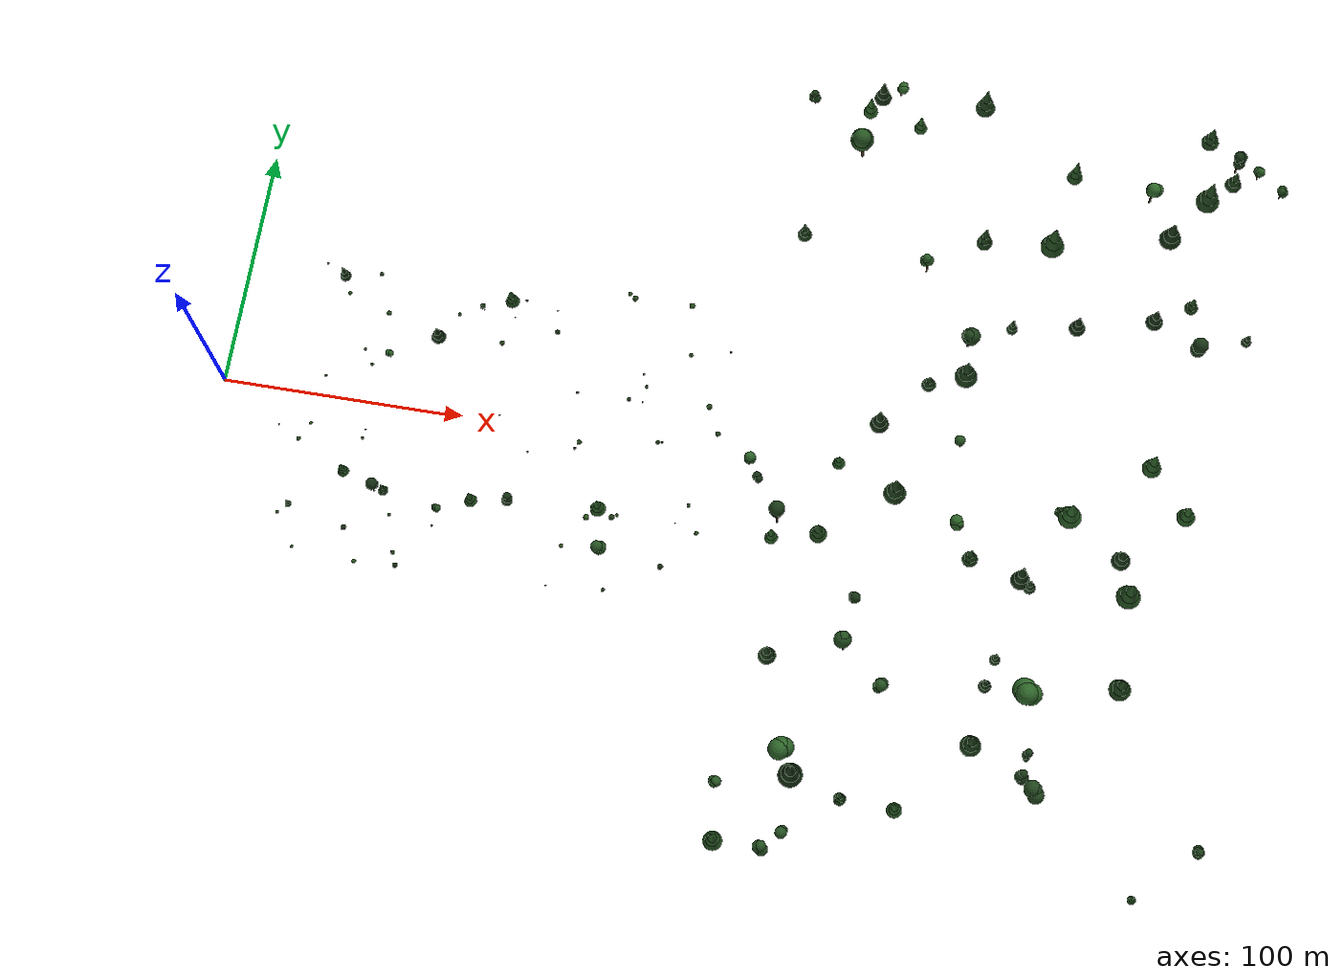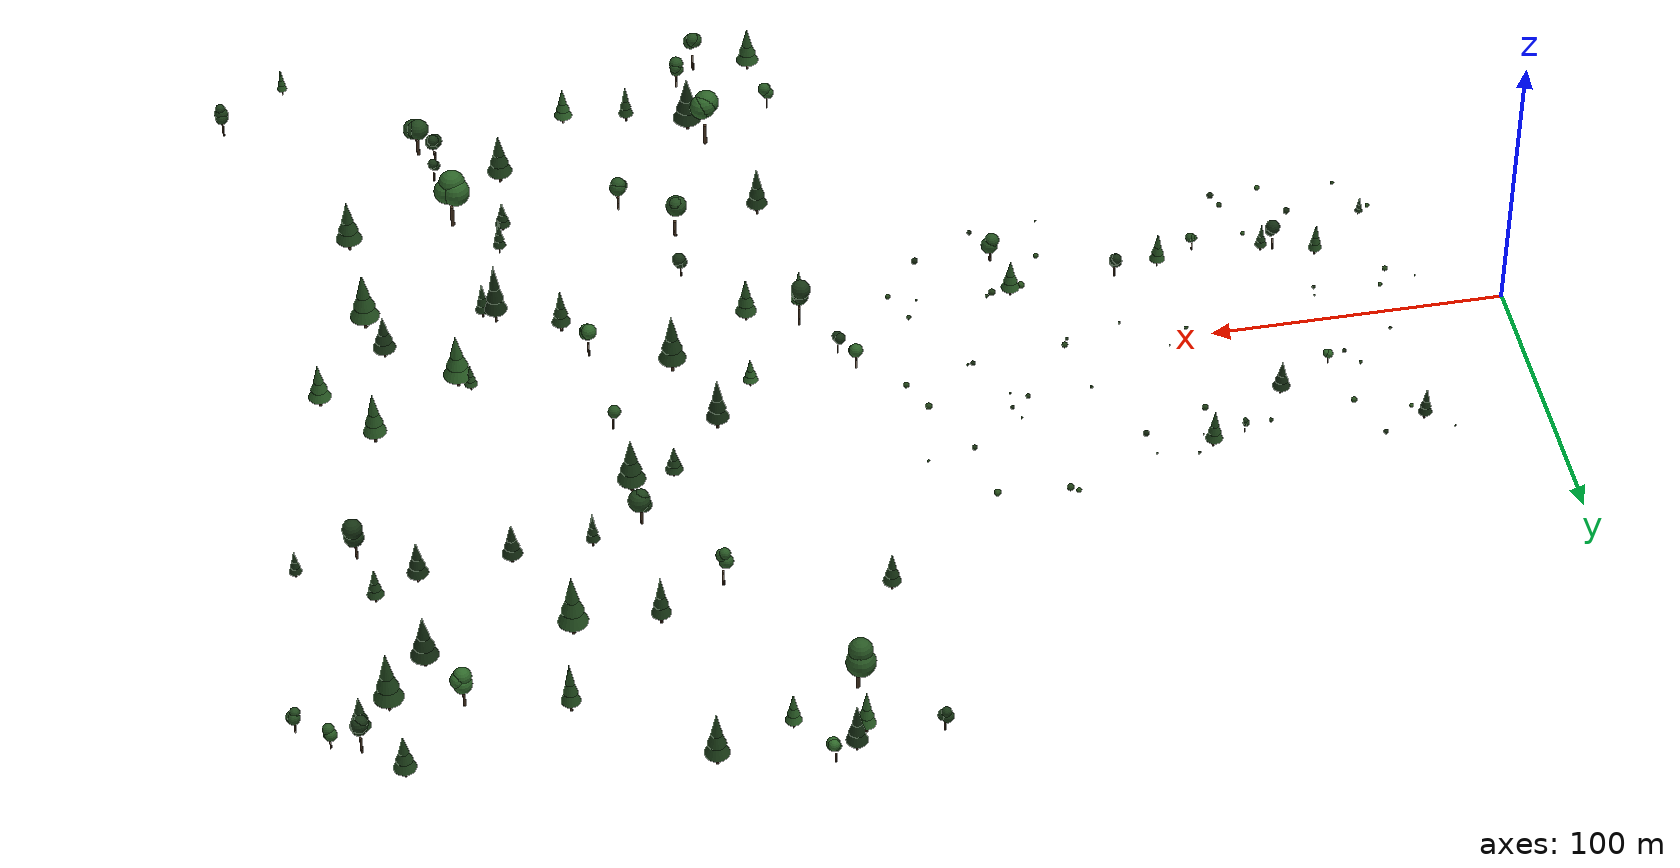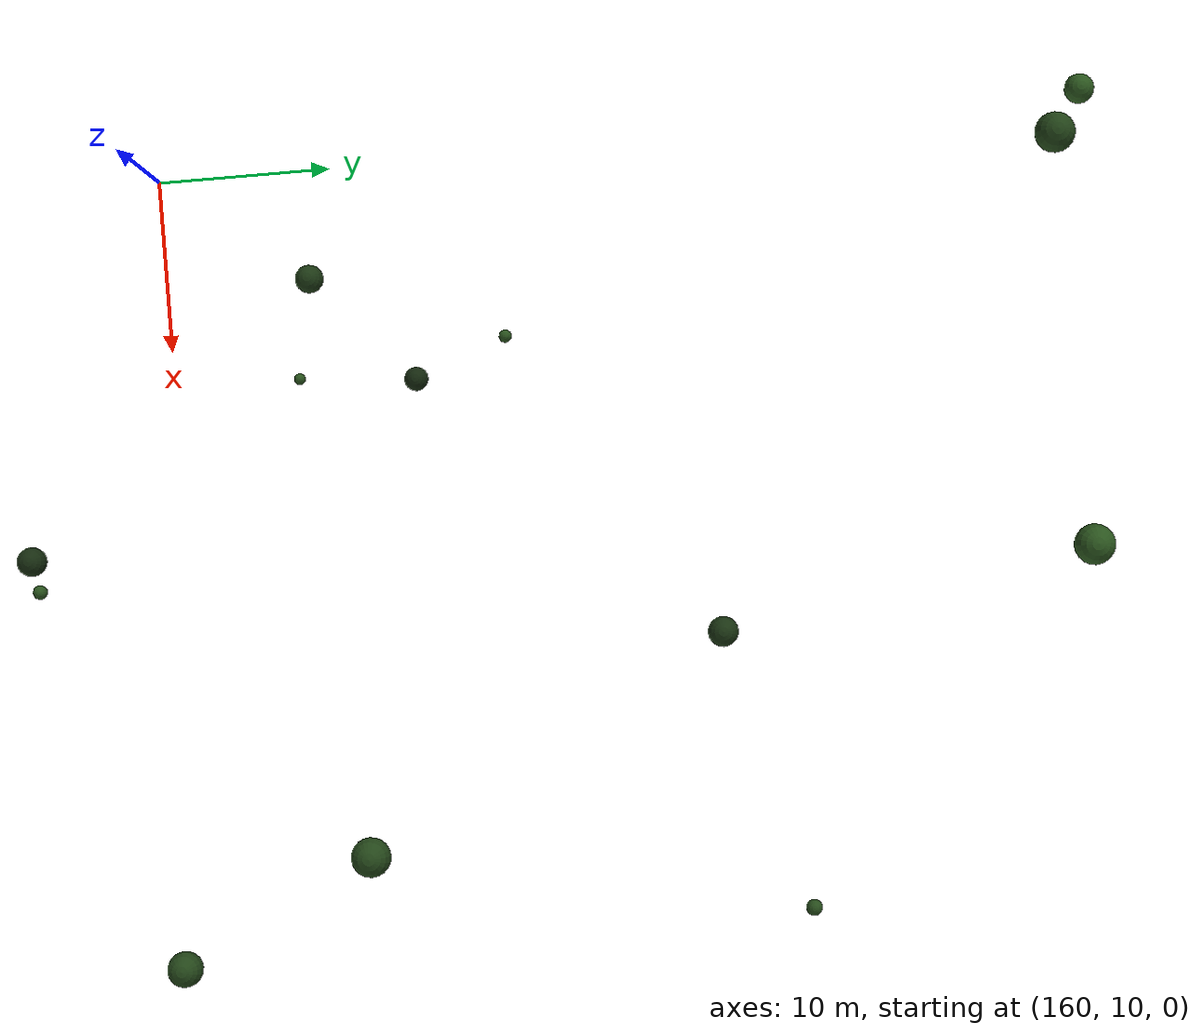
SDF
<sdf version="1.9">
 <world name="detection_world_terrain">
  <physics type="ode">
   <max_step_size>0.004</max_step_size>
   <real_time_factor>1.0</real_time_factor>
   <real_time_update_rate>250</real_time_update_rate>
  </physics>
  <gravity>0 0 -9.8</gravity>
  <magnetic_field>6e-06 2.3e-05 -4.2e-05</magnetic_field>
  <atmosphere type="adiabatic"><temperature>288</temperature></atmosphere>
  <plugin filename="gz-sim-physics-system" name="gz::sim::systems::Physics"/>
  <plugin filename="gz-sim-user-commands-system" name="gz::sim::systems::UserCommands"/>
  <plugin filename="gz-sim-scene-broadcaster-system" name="gz::sim::systems::SceneBroadcaster"/>
  <plugin filename="gz-sim-sensors-system" name="gz::sim::systems::Sensors">
   <render_engine>ogre2</render_engine>
  </plugin>
  <plugin filename="gz-sim-imu-system" name="gz::sim::systems::Imu"/>
  <plugin filename="gz-sim-magnetometer-system" name="gz::sim::systems::Magnetometer"/>
  <plugin filename="gz-sim-air-pressure-system" name="gz::sim::systems::AirPressure"/>
  <plugin filename="gz-sim-navsat-system" name="gz::sim::systems::NavSat"/>
  <scene>
   <grid>false</grid>
   <ambient>0.4 0.4 0.4 1</ambient>
   <background>0.55 0.7 0.9 1</background>
   <shadows>true</shadows>
  </scene>
  <light name="sunUTC" type="directional">
   <pose>0 0 500 0 -0 0</pose>
   <intensity>1</intensity>
   <direction>0.001 0.625 -0.78</direction>
   <diffuse>0.904 0.904 0.904 1</diffuse>
   <specular>0.271 0.271 0.271 1</specular>
   <attenuation><range>2000</range><linear>0</linear><constant>1</constant><quadratic>0</quadratic></attenuation>
  </light>
  <model name="detection_station">
   <static>true</static>
   <link name="base">
    <pose>0 0 0.5 0 0 0</pose>
    <visual name="cabin">
     <geometry><box><size>1.2 1.2 1.0</size></box></geometry>
     <material><ambient>0.3 0.3 0.32 1</ambient><diffuse>0.3 0.3 0.32 1</diffuse></material>
    </visual>
    <collision name="cabin_col"><geometry><box><size>1.2 1.2 1.0</size></box></geometry></collision>
   </link>
   <link name="mast">
    <pose>0 0 1.75 0 0 0</pose>
    <visual name="pole">
     <geometry><cylinder><radius>0.04</radius><length>1.5</length></cylinder></geometry>
     <material><ambient>0.5 0.5 0.5 1</ambient><diffuse>0.5 0.5 0.5 1</diffuse></material>
    </visual>
   </link>
   <link name="camera_link">
    <pose>0.1 0 2.5 0 -0.2269 0</pose>
    <visual name="camera_body">
     <geometry><box><size>0.12 0.08 0.08</size></box></geometry>
     <material><ambient>0.1 0.1 0.1 1</ambient><diffuse>0.1 0.1 0.1 1</diffuse></material>
    </visual>
    <sensor name="station_camera" type="camera">
     <topic>/detection_station/camera/image</topic>
     <update_rate>15</update_rate>
     <always_on>true</always_on>
     <visualize>false</visualize>
     <camera>
      <horizontal_fov>1.047</horizontal_fov>
      <image><width>1280</width><height>720</height><format>R8G8B8</format></image>
      <clip><near>0.1</near><far>2000</far></clip>
      <camera_info_topic>/detection_station/camera/camera_info</camera_info_topic>
     </camera>
    </sensor>
    <sensor name="station_zoom" type="camera">
     <topic>/detection_station/zoom/image</topic>
     <update_rate>15</update_rate>
     <always_on>true</always_on>
     <visualize>false</visualize>
     <camera>
      <horizontal_fov>0.10472</horizontal_fov>
      <image><width>1280</width><height>720</height><format>R8G8B8</format></image>
      <clip><near>0.1</near><far>2000</far></clip>
      <camera_info_topic>/detection_station/zoom/camera_info</camera_info_topic>
     </camera>
    </sensor>
    <sensor name="station_thermal" type="thermal">
     <topic>/detection_station/thermal/image</topic>
     <update_rate>15</update_rate>
     <always_on>true</always_on>
     <visualize>false</visualize>
     <camera>
      <horizontal_fov>0.4189</horizontal_fov>
      <image><width>640</width><height>512</height><format>L16</format></image>
      <clip><near>0.1</near><far>2000</far></clip>
     </camera>
     <plugin filename="gz-sim-thermal-sensor-system" name="gz::sim::systems::ThermalSensor">
      <min_temp>253.15</min_temp>
      <max_temp>673.15</max_temp>
      <resolution>0.01</resolution>
     </plugin>
    </sensor>
   </link>
   <link name="mic_array_link">
    <pose>0 0.35 1.1 0 0 0</pose>
    <visual name="mic_array">
     <geometry><cylinder><radius>0.09</radius><length>0.06</length></cylinder></geometry>
     <material><ambient>0.15 0.15 0.4 1</ambient><diffuse>0.15 0.15 0.4 1</diffuse></material>
    </visual>
   </link>
   <link name="radar_link">
    <pose>0.15 -0.35 1.3 0 -0.1 0</pose>
    <visual name="radar_panel">
     <geometry><box><size>0.04 0.5 0.4</size></box></geometry>
     <material><ambient>0.6 0.6 0.62 1</ambient><diffuse>0.6 0.6 0.62 1</diffuse></material>
    </visual>
   </link>
  </model>
  <spherical_coordinates>
   <surface_model>EARTH_WGS84</surface_model>
   <world_frame_orientation>ENU</world_frame_orientation>
   <latitude_deg>47.397971057728974</latitude_deg>
   <longitude_deg>8.546163739800146</longitude_deg>
   <elevation>0</elevation>
  </spherical_coordinates>
  <model name="tree_0">
   <static>true</static>
   <pose>388.88 87.70 16.57 0 0 4.92</pose>
   <link name="link">
    <visual name="trunk">
     <pose>0 0 2.38 0 0 0</pose>
     <geometry><cylinder><radius>0.33</radius><length>4.77</length></cylinder></geometry>
     <material><ambient>0.28 0.2 0.12 1</ambient><diffuse>0.28 0.2 0.12 1</diffuse></material>
    </visual>
    <visual name="canopy0">
     <pose>0 0 6.13 0 0 0</pose>
     <geometry><cone><radius>2.74</radius><length>5.72</length></cone></geometry>
     <material><ambient>0.125 0.277 0.111 1</ambient><diffuse>0.125 0.277 0.111 1</diffuse></material>
    </visual>
    <visual name="canopy1">
     <pose>0 0 8.86 0 0 0</pose>
     <geometry><cone><radius>2.05</radius><length>5.72</length></cone></geometry>
     <material><ambient>0.125 0.277 0.111 1</ambient><diffuse>0.125 0.277 0.111 1</diffuse></material>
    </visual>
    <visual name="canopy2">
     <pose>0 0 11.58 0 0 0</pose>
     <geometry><cone><radius>1.23</radius><length>5.72</length></cone></geometry>
     <material><ambient>0.125 0.277 0.111 1</ambient><diffuse>0.125 0.277 0.111 1</diffuse></material>
    </visual>
   </link>
  </model>
  <model name="tree_1">
   <static>true</static>
   <pose>280.66 -7.96 7.31 0 0 4.75</pose>
   <link name="link">
    <visual name="trunk">
     <pose>0 0 3.97 0 0 0</pose>
     <geometry><cylinder><radius>0.55</radius><length>7.95</length></cylinder></geometry>
     <material><ambient>0.28 0.2 0.12 1</ambient><diffuse>0.28 0.2 0.12 1</diffuse></material>
    </visual>
    <visual name="canopy0">
     <pose>0 0 10.22 0 0 0</pose>
     <geometry><cone><radius>4.55</radius><length>9.54</length></cone></geometry>
     <material><ambient>0.111 0.248 0.099 1</ambient><diffuse>0.111 0.248 0.099 1</diffuse></material>
    </visual>
    <visual name="canopy1">
     <pose>0 0 14.76 0 0 0</pose>
     <geometry><cone><radius>3.41</radius><length>9.54</length></cone></geometry>
     <material><ambient>0.111 0.248 0.099 1</ambient><diffuse>0.111 0.248 0.099 1</diffuse></material>
    </visual>
    <visual name="canopy2">
     <pose>0 0 19.31 0 0 0</pose>
     <geometry><cone><radius>2.05</radius><length>9.54</length></cone></geometry>
     <material><ambient>0.111 0.248 0.099 1</ambient><diffuse>0.111 0.248 0.099 1</diffuse></material>
    </visual>
   </link>
  </model>
  <model name="tree_2">
   <static>true</static>
   <pose>343.67 -84.83 13.31 0 0 1.64</pose>
   <link name="link">
    <visual name="trunk">
     <pose>0 0 4.16 0 0 0</pose>
     <geometry><cylinder><radius>0.64</radius><length>8.32</length></cylinder></geometry>
     <material><ambient>0.28 0.2 0.12 1</ambient><diffuse>0.28 0.2 0.12 1</diffuse></material>
    </visual>
    <visual name="canopy0">
     <pose>-0.61 0.74 18.41 0 0 0</pose>
     <geometry><sphere><radius>4.48</radius></sphere></geometry>
     <material><ambient>0.178 0.397 0.159 1</ambient><diffuse>0.178 0.397 0.159 1</diffuse></material>
    </visual>
    <visual name="canopy1">
     <pose>-0.09 -1.28 15.65 0 0 0</pose>
     <geometry><sphere><radius>4.35</radius></sphere></geometry>
     <material><ambient>0.178 0.397 0.159 1</ambient><diffuse>0.178 0.397 0.159 1</diffuse></material>
    </visual>
    <visual name="canopy2">
     <pose>1.32 1.50 15.90 0 0 0</pose>
     <geometry><sphere><radius>4.82</radius></sphere></geometry>
     <material><ambient>0.178 0.397 0.159 1</ambient><diffuse>0.178 0.397 0.159 1</diffuse></material>
    </visual>
   </link>
  </model>
  <model name="tree_3">
   <static>true</static>
   <pose>381.01 16.56 16.05 0 0 4.20</pose>
   <link name="link">
    <visual name="trunk">
     <pose>0 0 3.51 0 0 0</pose>
     <geometry><cylinder><radius>0.46</radius><length>7.03</length></cylinder></geometry>
     <material><ambient>0.28 0.2 0.12 1</ambient><diffuse>0.28 0.2 0.12 1</diffuse></material>
    </visual>
    <visual name="canopy0">
     <pose>0 0 9.03 0 0 0</pose>
     <geometry><cone><radius>3.85</radius><length>8.43</length></cone></geometry>
     <material><ambient>0.170 0.378 0.151 1</ambient><diffuse>0.170 0.378 0.151 1</diffuse></material>
    </visual>
    <visual name="canopy1">
     <pose>0 0 13.05 0 0 0</pose>
     <geometry><cone><radius>2.89</radius><length>8.43</length></cone></geometry>
     <material><ambient>0.170 0.378 0.151 1</ambient><diffuse>0.170 0.378 0.151 1</diffuse></material>
    </visual>
    <visual name="canopy2">
     <pose>0 0 17.06 0 0 0</pose>
     <geometry><cone><radius>1.73</radius><length>8.43</length></cone></geometry>
     <material><ambient>0.170 0.378 0.151 1</ambient><diffuse>0.170 0.378 0.151 1</diffuse></material>
    </visual>
   </link>
  </model>
  <model name="tree_4">
   <static>true</static>
   <pose>220.23 -2.18 3.32 0 0 4.44</pose>
   <link name="link">
    <visual name="trunk">
     <pose>0 0 2.35 0 0 0</pose>
     <geometry><cylinder><radius>0.30</radius><length>4.70</length></cylinder></geometry>
     <material><ambient>0.28 0.2 0.12 1</ambient><diffuse>0.28 0.2 0.12 1</diffuse></material>
    </visual>
    <visual name="canopy0">
     <pose>-0.46 0.10 8.18 0 0 0</pose>
     <geometry><sphere><radius>2.34</radius></sphere></geometry>
     <material><ambient>0.175 0.389 0.156 1</ambient><diffuse>0.175 0.389 0.156 1</diffuse></material>
    </visual>
    <visual name="canopy1">
     <pose>0.45 -0.08 7.65 0 0 0</pose>
     <geometry><sphere><radius>1.78</radius></sphere></geometry>
     <material><ambient>0.175 0.389 0.156 1</ambient><diffuse>0.175 0.389 0.156 1</diffuse></material>
    </visual>
    <visual name="canopy2">
     <pose>0.01 0.65 7.74 0 0 0</pose>
     <geometry><sphere><radius>1.98</radius></sphere></geometry>
     <material><ambient>0.175 0.389 0.156 1</ambient><diffuse>0.175 0.389 0.156 1</diffuse></material>
    </visual>
   </link>
  </model>
  <model name="tree_5">
   <static>true</static>
   <pose>329.49 106.92 10.80 0 0 2.79</pose>
   <link name="link">
    <visual name="trunk">
     <pose>0 0 4.11 0 0 0</pose>
     <geometry><cylinder><radius>0.59</radius><length>8.22</length></cylinder></geometry>
     <material><ambient>0.28 0.2 0.12 1</ambient><diffuse>0.28 0.2 0.12 1</diffuse></material>
    </visual>
    <visual name="canopy0">
     <pose>0 0 10.57 0 0 0</pose>
     <geometry><cone><radius>4.89</radius><length>9.87</length></cone></geometry>
     <material><ambient>0.144 0.321 0.128 1</ambient><diffuse>0.144 0.321 0.128 1</diffuse></material>
    </visual>
    <visual name="canopy1">
     <pose>0 0 15.27 0 0 0</pose>
     <geometry><cone><radius>3.67</radius><length>9.87</length></cone></geometry>
     <material><ambient>0.144 0.321 0.128 1</ambient><diffuse>0.144 0.321 0.128 1</diffuse></material>
    </visual>
    <visual name="canopy2">
     <pose>0 0 19.97 0 0 0</pose>
     <geometry><cone><radius>2.20</radius><length>9.87</length></cone></geometry>
     <material><ambient>0.144 0.321 0.128 1</ambient><diffuse>0.144 0.321 0.128 1</diffuse></material>
    </visual>
   </link>
  </model>
  <model name="tree_6">
   <static>true</static>
   <pose>339.26 -39.13 12.38 0 0 3.85</pose>
   <link name="link">
    <visual name="trunk">
     <pose>0 0 2.46 0 0 0</pose>
     <geometry><cylinder><radius>0.30</radius><length>4.92</length></cylinder></geometry>
     <material><ambient>0.28 0.2 0.12 1</ambient><diffuse>0.28 0.2 0.12 1</diffuse></material>
    </visual>
    <visual name="canopy0">
     <pose>0 0 6.33 0 0 0</pose>
     <geometry><cone><radius>2.46</radius><length>5.91</length></cone></geometry>
     <material><ambient>0.101 0.225 0.090 1</ambient><diffuse>0.101 0.225 0.090 1</diffuse></material>
    </visual>
    <visual name="canopy1">
     <pose>0 0 9.14 0 0 0</pose>
     <geometry><cone><radius>1.85</radius><length>5.91</length></cone></geometry>
     <material><ambient>0.101 0.225 0.090 1</ambient><diffuse>0.101 0.225 0.090 1</diffuse></material>
    </visual>
    <visual name="canopy2">
     <pose>0 0 11.95 0 0 0</pose>
     <geometry><cone><radius>1.11</radius><length>5.91</length></cone></geometry>
     <material><ambient>0.101 0.225 0.090 1</ambient><diffuse>0.101 0.225 0.090 1</diffuse></material>
    </visual>
   </link>
  </model>
  <model name="tree_7">
   <static>true</static>
   <pose>351.33 -7.98 12.77 0 0 5.29</pose>
   <link name="link">
    <visual name="trunk">
     <pose>0 0 3.61 0 0 0</pose>
     <geometry><cylinder><radius>0.57</radius><length>7.21</length></cylinder></geometry>
     <material><ambient>0.28 0.2 0.12 1</ambient><diffuse>0.28 0.2 0.12 1</diffuse></material>
    </visual>
    <visual name="canopy0">
     <pose>0 0 9.27 0 0 0</pose>
     <geometry><cone><radius>4.74</radius><length>8.65</length></cone></geometry>
     <material><ambient>0.181 0.402 0.161 1</ambient><diffuse>0.181 0.402 0.161 1</diffuse></material>
    </visual>
    <visual name="canopy1">
     <pose>0 0 13.39 0 0 0</pose>
     <geometry><cone><radius>3.56</radius><length>8.65</length></cone></geometry>
     <material><ambient>0.181 0.402 0.161 1</ambient><diffuse>0.181 0.402 0.161 1</diffuse></material>
    </visual>
    <visual name="canopy2">
     <pose>0 0 17.52 0 0 0</pose>
     <geometry><cone><radius>2.13</radius><length>8.65</length></cone></geometry>
     <material><ambient>0.181 0.402 0.161 1</ambient><diffuse>0.181 0.402 0.161 1</diffuse></material>
    </visual>
   </link>
  </model>
  <model name="tree_8">
   <static>true</static>
   <pose>399.63 143.85 18.35 0 0 5.10</pose>
   <link name="link">
    <visual name="trunk">
     <pose>0 0 2.71 0 0 0</pose>
     <geometry><cylinder><radius>0.40</radius><length>5.42</length></cylinder></geometry>
     <material><ambient>0.28 0.2 0.12 1</ambient><diffuse>0.28 0.2 0.12 1</diffuse></material>
    </visual>
    <visual name="canopy0">
     <pose>0 0 6.97 0 0 0</pose>
     <geometry><cone><radius>3.35</radius><length>6.50</length></cone></geometry>
     <material><ambient>0.111 0.246 0.098 1</ambient><diffuse>0.111 0.246 0.098 1</diffuse></material>
    </visual>
    <visual name="canopy1">
     <pose>0 0 10.06 0 0 0</pose>
     <geometry><cone><radius>2.51</radius><length>6.50</length></cone></geometry>
     <material><ambient>0.111 0.246 0.098 1</ambient><diffuse>0.111 0.246 0.098 1</diffuse></material>
    </visual>
    <visual name="canopy2">
     <pose>0 0 13.16 0 0 0</pose>
     <geometry><cone><radius>1.51</radius><length>6.50</length></cone></geometry>
     <material><ambient>0.111 0.246 0.098 1</ambient><diffuse>0.111 0.246 0.098 1</diffuse></material>
    </visual>
   </link>
  </model>
  <model name="tree_9">
   <static>true</static>
   <pose>389.90 134.31 17.17 0 0 4.15</pose>
   <link name="link">
    <visual name="trunk">
     <pose>0 0 4.08 0 0 0</pose>
     <geometry><cylinder><radius>0.58</radius><length>8.15</length></cylinder></geometry>
     <material><ambient>0.28 0.2 0.12 1</ambient><diffuse>0.28 0.2 0.12 1</diffuse></material>
    </visual>
    <visual name="canopy0">
     <pose>0 0 10.48 0 0 0</pose>
     <geometry><cone><radius>4.81</radius><length>9.78</length></cone></geometry>
     <material><ambient>0.130 0.288 0.115 1</ambient><diffuse>0.130 0.288 0.115 1</diffuse></material>
    </visual>
    <visual name="canopy1">
     <pose>0 0 15.14 0 0 0</pose>
     <geometry><cone><radius>3.61</radius><length>9.78</length></cone></geometry>
     <material><ambient>0.130 0.288 0.115 1</ambient><diffuse>0.130 0.288 0.115 1</diffuse></material>
    </visual>
    <visual name="canopy2">
     <pose>0 0 19.80 0 0 0</pose>
     <geometry><cone><radius>2.16</radius><length>9.78</length></cone></geometry>
     <material><ambient>0.130 0.288 0.115 1</ambient><diffuse>0.130 0.288 0.115 1</diffuse></material>
    </visual>
   </link>
  </model>
  <model name="tree_10">
   <static>true</static>
   <pose>419.25 141.76 20.75 0 0 0.28</pose>
   <link name="link">
    <visual name="trunk">
     <pose>0 0 1.95 0 0 0</pose>
     <geometry><cylinder><radius>0.28</radius><length>3.90</length></cylinder></geometry>
     <material><ambient>0.28 0.2 0.12 1</ambient><diffuse>0.28 0.2 0.12 1</diffuse></material>
    </visual>
    <visual name="canopy0">
     <pose>0.18 0.48 6.81 0 0 0</pose>
     <geometry><sphere><radius>2.00</radius></sphere></geometry>
     <material><ambient>0.134 0.297 0.119 1</ambient><diffuse>0.134 0.297 0.119 1</diffuse></material>
    </visual>
    <visual name="canopy1">
     <pose>-0.54 -0.39 8.35 0 0 0</pose>
     <geometry><sphere><radius>1.67</radius></sphere></geometry>
     <material><ambient>0.134 0.297 0.119 1</ambient><diffuse>0.134 0.297 0.119 1</diffuse></material>
    </visual>
    <visual name="canopy2">
     <pose>0.44 -0.56 6.54 0 0 0</pose>
     <geometry><sphere><radius>1.97</radius></sphere></geometry>
     <material><ambient>0.134 0.297 0.119 1</ambient><diffuse>0.134 0.297 0.119 1</diffuse></material>
    </visual>
   </link>
  </model>
  <model name="tree_11">
   <static>true</static>
   <pose>334.77 139.41 11.02 0 0 3.81</pose>
   <link name="link">
    <visual name="trunk">
     <pose>0 0 3.42 0 0 0</pose>
     <geometry><cylinder><radius>0.38</radius><length>6.83</length></cylinder></geometry>
     <material><ambient>0.28 0.2 0.12 1</ambient><diffuse>0.28 0.2 0.12 1</diffuse></material>
    </visual>
    <visual name="canopy0">
     <pose>0 0 8.79 0 0 0</pose>
     <geometry><cone><radius>3.17</radius><length>8.20</length></cone></geometry>
     <material><ambient>0.150 0.332 0.133 1</ambient><diffuse>0.150 0.332 0.133 1</diffuse></material>
    </visual>
    <visual name="canopy1">
     <pose>0 0 12.69 0 0 0</pose>
     <geometry><cone><radius>2.37</radius><length>8.20</length></cone></geometry>
     <material><ambient>0.150 0.332 0.133 1</ambient><diffuse>0.150 0.332 0.133 1</diffuse></material>
    </visual>
    <visual name="canopy2">
     <pose>0 0 16.60 0 0 0</pose>
     <geometry><cone><radius>1.42</radius><length>8.20</length></cone></geometry>
     <material><ambient>0.150 0.332 0.133 1</ambient><diffuse>0.150 0.332 0.133 1</diffuse></material>
    </visual>
   </link>
  </model>
  <model name="tree_12">
   <static>true</static>
   <pose>335.19 -36.99 11.69 0 0 6.04</pose>
   <link name="link">
    <visual name="trunk">
     <pose>0 0 4.15 0 0 0</pose>
     <geometry><cylinder><radius>0.46</radius><length>8.30</length></cylinder></geometry>
     <material><ambient>0.28 0.2 0.12 1</ambient><diffuse>0.28 0.2 0.12 1</diffuse></material>
    </visual>
    <visual name="canopy0">
     <pose>0 0 10.68 0 0 0</pose>
     <geometry><cone><radius>3.87</radius><length>9.97</length></cone></geometry>
     <material><ambient>0.083 0.185 0.074 1</ambient><diffuse>0.083 0.185 0.074 1</diffuse></material>
    </visual>
    <visual name="canopy1">
     <pose>0 0 15.42 0 0 0</pose>
     <geometry><cone><radius>2.90</radius><length>9.97</length></cone></geometry>
     <material><ambient>0.083 0.185 0.074 1</ambient><diffuse>0.083 0.185 0.074 1</diffuse></material>
    </visual>
    <visual name="canopy2">
     <pose>0 0 20.17 0 0 0</pose>
     <geometry><cone><radius>1.74</radius><length>9.97</length></cone></geometry>
     <material><ambient>0.083 0.185 0.074 1</ambient><diffuse>0.083 0.185 0.074 1</diffuse></material>
    </visual>
   </link>
  </model>
  <model name="tree_13">
   <static>true</static>
   <pose>256.99 -127.88 5.64 0 0 2.67</pose>
   <link name="link">
    <visual name="trunk">
     <pose>0 0 3.71 0 0 0</pose>
     <geometry><cylinder><radius>0.60</radius><length>7.42</length></cylinder></geometry>
     <material><ambient>0.28 0.2 0.12 1</ambient><diffuse>0.28 0.2 0.12 1</diffuse></material>
    </visual>
    <visual name="canopy0">
     <pose>0 0 9.54 0 0 0</pose>
     <geometry><cone><radius>4.98</radius><length>8.91</length></cone></geometry>
     <material><ambient>0.083 0.185 0.074 1</ambient><diffuse>0.083 0.185 0.074 1</diffuse></material>
    </visual>
    <visual name="canopy1">
     <pose>0 0 13.79 0 0 0</pose>
     <geometry><cone><radius>3.74</radius><length>8.91</length></cone></geometry>
     <material><ambient>0.083 0.185 0.074 1</ambient><diffuse>0.083 0.185 0.074 1</diffuse></material>
    </visual>
    <visual name="canopy2">
     <pose>0 0 18.03 0 0 0</pose>
     <geometry><cone><radius>2.24</radius><length>8.91</length></cone></geometry>
     <material><ambient>0.083 0.185 0.074 1</ambient><diffuse>0.083 0.185 0.074 1</diffuse></material>
    </visual>
   </link>
  </model>
  <model name="tree_14">
   <static>true</static>
   <pose>240.30 -81.63 4.62 0 0 3.16</pose>
   <link name="link">
    <visual name="trunk">
     <pose>0 0 3.33 0 0 0</pose>
     <geometry><cylinder><radius>0.43</radius><length>6.67</length></cylinder></geometry>
     <material><ambient>0.28 0.2 0.12 1</ambient><diffuse>0.28 0.2 0.12 1</diffuse></material>
    </visual>
    <visual name="canopy0">
     <pose>0 0 8.58 0 0 0</pose>
     <geometry><cone><radius>3.58</radius><length>8.00</length></cone></geometry>
     <material><ambient>0.100 0.223 0.089 1</ambient><diffuse>0.100 0.223 0.089 1</diffuse></material>
    </visual>
    <visual name="canopy1">
     <pose>0 0 12.39 0 0 0</pose>
     <geometry><cone><radius>2.69</radius><length>8.00</length></cone></geometry>
     <material><ambient>0.100 0.223 0.089 1</ambient><diffuse>0.100 0.223 0.089 1</diffuse></material>
    </visual>
    <visual name="canopy2">
     <pose>0 0 16.20 0 0 0</pose>
     <geometry><cone><radius>1.61</radius><length>8.00</length></cone></geometry>
     <material><ambient>0.100 0.223 0.089 1</ambient><diffuse>0.100 0.223 0.089 1</diffuse></material>
    </visual>
   </link>
  </model>
  <model name="tree_15">
   <static>true</static>
   <pose>227.88 -135.69 3.73 0 0 1.10</pose>
   <link name="link">
    <visual name="trunk">
     <pose>0 0 2.24 0 0 0</pose>
     <geometry><cylinder><radius>0.29</radius><length>4.48</length></cylinder></geometry>
     <material><ambient>0.28 0.2 0.12 1</ambient><diffuse>0.28 0.2 0.12 1</diffuse></material>
    </visual>
    <visual name="canopy0">
     <pose>0.49 0.61 7.58 0 0 0</pose>
     <geometry><sphere><radius>2.02</radius></sphere></geometry>
     <material><ambient>0.160 0.356 0.142 1</ambient><diffuse>0.160 0.356 0.142 1</diffuse></material>
    </visual>
    <visual name="canopy1">
     <pose>0.68 -0.64 9.20 0 0 0</pose>
     <geometry><sphere><radius>2.16</radius></sphere></geometry>
     <material><ambient>0.160 0.356 0.142 1</ambient><diffuse>0.160 0.356 0.142 1</diffuse></material>
    </visual>
    <visual name="canopy2">
     <pose>-0.23 -0.36 8.94 0 0 0</pose>
     <geometry><sphere><radius>1.82</radius></sphere></geometry>
     <material><ambient>0.160 0.356 0.142 1</ambient><diffuse>0.160 0.356 0.142 1</diffuse></material>
    </visual>
   </link>
  </model>
  <model name="tree_16">
   <static>true</static>
   <pose>314.33 -30.63 9.79 0 0 5.26</pose>
   <link name="link">
    <visual name="trunk">
     <pose>0 0 3.00 0 0 0</pose>
     <geometry><cylinder><radius>0.38</radius><length>5.99</length></cylinder></geometry>
     <material><ambient>0.28 0.2 0.12 1</ambient><diffuse>0.28 0.2 0.12 1</diffuse></material>
    </visual>
    <visual name="canopy0">
     <pose>0 0 7.70 0 0 0</pose>
     <geometry><cone><radius>3.17</radius><length>7.19</length></cone></geometry>
     <material><ambient>0.120 0.266 0.106 1</ambient><diffuse>0.120 0.266 0.106 1</diffuse></material>
    </visual>
    <visual name="canopy1">
     <pose>0 0 11.13 0 0 0</pose>
     <geometry><cone><radius>2.37</radius><length>7.19</length></cone></geometry>
     <material><ambient>0.120 0.266 0.106 1</ambient><diffuse>0.120 0.266 0.106 1</diffuse></material>
    </visual>
    <visual name="canopy2">
     <pose>0 0 14.55 0 0 0</pose>
     <geometry><cone><radius>1.42</radius><length>7.19</length></cone></geometry>
     <material><ambient>0.120 0.266 0.106 1</ambient><diffuse>0.120 0.266 0.106 1</diffuse></material>
    </visual>
   </link>
  </model>
  <model name="tree_17">
   <static>true</static>
   <pose>270.19 20.60 6.46 0 0 1.76</pose>
   <link name="link">
    <visual name="trunk">
     <pose>0 0 3.57 0 0 0</pose>
     <geometry><cylinder><radius>0.46</radius><length>7.13</length></cylinder></geometry>
     <material><ambient>0.28 0.2 0.12 1</ambient><diffuse>0.28 0.2 0.12 1</diffuse></material>
    </visual>
    <visual name="canopy0">
     <pose>0 0 9.17 0 0 0</pose>
     <geometry><cone><radius>3.81</radius><length>8.56</length></cone></geometry>
     <material><ambient>0.086 0.191 0.076 1</ambient><diffuse>0.086 0.191 0.076 1</diffuse></material>
    </visual>
    <visual name="canopy1">
     <pose>0 0 13.25 0 0 0</pose>
     <geometry><cone><radius>2.86</radius><length>8.56</length></cone></geometry>
     <material><ambient>0.086 0.191 0.076 1</ambient><diffuse>0.086 0.191 0.076 1</diffuse></material>
    </visual>
    <visual name="canopy2">
     <pose>0 0 17.32 0 0 0</pose>
     <geometry><cone><radius>1.71</radius><length>8.56</length></cone></geometry>
     <material><ambient>0.086 0.191 0.076 1</ambient><diffuse>0.086 0.191 0.076 1</diffuse></material>
    </visual>
   </link>
  </model>
  <model name="tree_18">
   <static>true</static>
   <pose>268.03 154.06 6.07 0 0 3.98</pose>
   <link name="link">
    <visual name="trunk">
     <pose>0 0 2.46 0 0 0</pose>
     <geometry><cylinder><radius>0.32</radius><length>4.91</length></cylinder></geometry>
     <material><ambient>0.28 0.2 0.12 1</ambient><diffuse>0.28 0.2 0.12 1</diffuse></material>
    </visual>
    <visual name="canopy0">
     <pose>0 0 6.31 0 0 0</pose>
     <geometry><cone><radius>2.65</radius><length>5.89</length></cone></geometry>
     <material><ambient>0.183 0.407 0.163 1</ambient><diffuse>0.183 0.407 0.163 1</diffuse></material>
    </visual>
    <visual name="canopy1">
     <pose>0 0 9.12 0 0 0</pose>
     <geometry><cone><radius>1.99</radius><length>5.89</length></cone></geometry>
     <material><ambient>0.183 0.407 0.163 1</ambient><diffuse>0.183 0.407 0.163 1</diffuse></material>
    </visual>
    <visual name="canopy2">
     <pose>0 0 11.93 0 0 0</pose>
     <geometry><cone><radius>1.19</radius><length>5.89</length></cone></geometry>
     <material><ambient>0.183 0.407 0.163 1</ambient><diffuse>0.183 0.407 0.163 1</diffuse></material>
    </visual>
   </link>
  </model>
  <model name="tree_19">
   <static>true</static>
   <pose>344.22 73.31 11.32 0 0 1.21</pose>
   <link name="link">
    <visual name="trunk">
     <pose>0 0 2.77 0 0 0</pose>
     <geometry><cylinder><radius>0.40</radius><length>5.53</length></cylinder></geometry>
     <material><ambient>0.28 0.2 0.12 1</ambient><diffuse>0.28 0.2 0.12 1</diffuse></material>
    </visual>
    <visual name="canopy0">
     <pose>0 0 7.11 0 0 0</pose>
     <geometry><cone><radius>3.35</radius><length>6.64</length></cone></geometry>
     <material><ambient>0.081 0.180 0.072 1</ambient><diffuse>0.081 0.180 0.072 1</diffuse></material>
    </visual>
    <visual name="canopy1">
     <pose>0 0 10.27 0 0 0</pose>
     <geometry><cone><radius>2.51</radius><length>6.64</length></cone></geometry>
     <material><ambient>0.081 0.180 0.072 1</ambient><diffuse>0.081 0.180 0.072 1</diffuse></material>
    </visual>
    <visual name="canopy2">
     <pose>0 0 13.43 0 0 0</pose>
     <geometry><cone><radius>1.51</radius><length>6.64</length></cone></geometry>
     <material><ambient>0.081 0.180 0.072 1</ambient><diffuse>0.081 0.180 0.072 1</diffuse></material>
    </visual>
   </link>
  </model>
  <model name="tree_20">
   <static>true</static>
   <pose>286.88 -88.60 7.95 0 0 4.74</pose>
   <link name="link">
    <visual name="trunk">
     <pose>0 0 2.68 0 0 0</pose>
     <geometry><cylinder><radius>0.42</radius><length>5.36</length></cylinder></geometry>
     <material><ambient>0.28 0.2 0.12 1</ambient><diffuse>0.28 0.2 0.12 1</diffuse></material>
    </visual>
    <visual name="canopy0">
     <pose>-0.18 -0.21 11.10 0 0 0</pose>
     <geometry><sphere><radius>2.63</radius></sphere></geometry>
     <material><ambient>0.142 0.316 0.127 1</ambient><diffuse>0.142 0.316 0.127 1</diffuse></material>
    </visual>
    <visual name="canopy1">
     <pose>0.34 -0.96 10.12 0 0 0</pose>
     <geometry><sphere><radius>2.43</radius></sphere></geometry>
     <material><ambient>0.142 0.316 0.127 1</ambient><diffuse>0.142 0.316 0.127 1</diffuse></material>
    </visual>
    <visual name="canopy2">
     <pose>-0.72 0.06 10.28 0 0 0</pose>
     <geometry><sphere><radius>2.80</radius></sphere></geometry>
     <material><ambient>0.142 0.316 0.127 1</ambient><diffuse>0.142 0.316 0.127 1</diffuse></material>
    </visual>
   </link>
  </model>
  <model name="tree_21">
   <static>true</static>
   <pose>396.78 -1.84 17.58 0 0 5.10</pose>
   <link name="link">
    <visual name="trunk">
     <pose>0 0 2.89 0 0 0</pose>
     <geometry><cylinder><radius>0.45</radius><length>5.79</length></cylinder></geometry>
     <material><ambient>0.28 0.2 0.12 1</ambient><diffuse>0.28 0.2 0.12 1</diffuse></material>
    </visual>
    <visual name="canopy0">
     <pose>0 0 7.44 0 0 0</pose>
     <geometry><cone><radius>3.72</radius><length>6.95</length></cone></geometry>
     <material><ambient>0.176 0.390 0.156 1</ambient><diffuse>0.176 0.390 0.156 1</diffuse></material>
    </visual>
    <visual name="canopy1">
     <pose>0 0 10.75 0 0 0</pose>
     <geometry><cone><radius>2.79</radius><length>6.95</length></cone></geometry>
     <material><ambient>0.176 0.390 0.156 1</ambient><diffuse>0.176 0.390 0.156 1</diffuse></material>
    </visual>
    <visual name="canopy2">
     <pose>0 0 14.06 0 0 0</pose>
     <geometry><cone><radius>1.67</radius><length>6.95</length></cone></geometry>
     <material><ambient>0.176 0.390 0.156 1</ambient><diffuse>0.176 0.390 0.156 1</diffuse></material>
    </visual>
   </link>
  </model>
  <model name="tree_22">
   <static>true</static>
   <pose>257.60 169.80 5.21 0 0 1.76</pose>
   <link name="link">
    <visual name="trunk">
     <pose>0 0 1.95 0 0 0</pose>
     <geometry><cylinder><radius>0.29</radius><length>3.91</length></cylinder></geometry>
     <material><ambient>0.28 0.2 0.12 1</ambient><diffuse>0.28 0.2 0.12 1</diffuse></material>
    </visual>
    <visual name="canopy0">
     <pose>-0.14 0.26 7.03 0 0 0</pose>
     <geometry><sphere><radius>1.64</radius></sphere></geometry>
     <material><ambient>0.188 0.417 0.167 1</ambient><diffuse>0.188 0.417 0.167 1</diffuse></material>
    </visual>
    <visual name="canopy1">
     <pose>0.32 -0.73 8.44 0 0 0</pose>
     <geometry><sphere><radius>1.91</radius></sphere></geometry>
     <material><ambient>0.188 0.417 0.167 1</ambient><diffuse>0.188 0.417 0.167 1</diffuse></material>
    </visual>
    <visual name="canopy2">
     <pose>-0.59 -0.56 7.96 0 0 0</pose>
     <geometry><sphere><radius>2.21</radius></sphere></geometry>
     <material><ambient>0.188 0.417 0.167 1</ambient><diffuse>0.188 0.417 0.167 1</diffuse></material>
    </visual>
   </link>
  </model>
  <model name="tree_23">
   <static>true</static>
   <pose>415.70 -135.94 20.66 0 0 3.51</pose>
   <link name="link">
    <visual name="trunk">
     <pose>0 0 2.72 0 0 0</pose>
     <geometry><cylinder><radius>0.31</radius><length>5.44</length></cylinder></geometry>
     <material><ambient>0.28 0.2 0.12 1</ambient><diffuse>0.28 0.2 0.12 1</diffuse></material>
    </visual>
    <visual name="canopy0">
     <pose>-0.07 0.45 11.90 0 0 0</pose>
     <geometry><sphere><radius>1.67</radius></sphere></geometry>
     <material><ambient>0.111 0.246 0.098 1</ambient><diffuse>0.111 0.246 0.098 1</diffuse></material>
    </visual>
    <visual name="canopy1">
     <pose>0.03 0.23 9.90 0 0 0</pose>
     <geometry><sphere><radius>2.34</radius></sphere></geometry>
     <material><ambient>0.111 0.246 0.098 1</ambient><diffuse>0.111 0.246 0.098 1</diffuse></material>
    </visual>
    <visual name="canopy2">
     <pose>-0.34 -0.75 8.71 0 0 0</pose>
     <geometry><sphere><radius>2.17</radius></sphere></geometry>
     <material><ambient>0.111 0.246 0.098 1</ambient><diffuse>0.111 0.246 0.098 1</diffuse></material>
    </visual>
   </link>
  </model>
  <model name="tree_24">
   <static>true</static>
   <pose>409.30 149.07 19.62 0 0 4.51</pose>
   <link name="link">
    <visual name="trunk">
     <pose>0 0 1.85 0 0 0</pose>
     <geometry><cylinder><radius>0.28</radius><length>3.71</length></cylinder></geometry>
     <material><ambient>0.28 0.2 0.12 1</ambient><diffuse>0.28 0.2 0.12 1</diffuse></material>
    </visual>
    <visual name="canopy0">
     <pose>0.22 0.30 8.21 0 0 0</pose>
     <geometry><sphere><radius>1.92</radius></sphere></geometry>
     <material><ambient>0.157 0.348 0.139 1</ambient><diffuse>0.157 0.348 0.139 1</diffuse></material>
    </visual>
    <visual name="canopy1">
     <pose>-0.18 0.05 6.37 0 0 0</pose>
     <geometry><sphere><radius>1.88</radius></sphere></geometry>
     <material><ambient>0.157 0.348 0.139 1</ambient><diffuse>0.157 0.348 0.139 1</diffuse></material>
    </visual>
    <visual name="canopy2">
     <pose>-0.69 -0.49 6.71 0 0 0</pose>
     <geometry><sphere><radius>2.04</radius></sphere></geometry>
     <material><ambient>0.157 0.348 0.139 1</ambient><diffuse>0.157 0.348 0.139 1</diffuse></material>
    </visual>
   </link>
  </model>
  <model name="tree_25">
   <static>true</static>
   <pose>287.65 40.98 7.52 0 0 2.48</pose>
   <link name="link">
    <visual name="trunk">
     <pose>0 0 2.15 0 0 0</pose>
     <geometry><cylinder><radius>0.35</radius><length>4.30</length></cylinder></geometry>
     <material><ambient>0.28 0.2 0.12 1</ambient><diffuse>0.28 0.2 0.12 1</diffuse></material>
    </visual>
    <visual name="canopy0">
     <pose>0 0 5.53 0 0 0</pose>
     <geometry><cone><radius>2.93</radius><length>5.16</length></cone></geometry>
     <material><ambient>0.112 0.249 0.100 1</ambient><diffuse>0.112 0.249 0.100 1</diffuse></material>
    </visual>
    <visual name="canopy1">
     <pose>0 0 7.99 0 0 0</pose>
     <geometry><cone><radius>2.20</radius><length>5.16</length></cone></geometry>
     <material><ambient>0.112 0.249 0.100 1</ambient><diffuse>0.112 0.249 0.100 1</diffuse></material>
    </visual>
    <visual name="canopy2">
     <pose>0 0 10.45 0 0 0</pose>
     <geometry><cone><radius>1.32</radius><length>5.16</length></cone></geometry>
     <material><ambient>0.112 0.249 0.100 1</ambient><diffuse>0.112 0.249 0.100 1</diffuse></material>
    </visual>
   </link>
  </model>
  <model name="tree_26">
   <static>true</static>
   <pose>329.70 -70.24 11.73 0 0 3.28</pose>
   <link name="link">
    <visual name="trunk">
     <pose>0 0 2.34 0 0 0</pose>
     <geometry><cylinder><radius>0.26</radius><length>4.67</length></cylinder></geometry>
     <material><ambient>0.28 0.2 0.12 1</ambient><diffuse>0.28 0.2 0.12 1</diffuse></material>
    </visual>
    <visual name="canopy0">
     <pose>0 0 6.01 0 0 0</pose>
     <geometry><cone><radius>2.19</radius><length>5.61</length></cone></geometry>
     <material><ambient>0.100 0.223 0.089 1</ambient><diffuse>0.100 0.223 0.089 1</diffuse></material>
    </visual>
    <visual name="canopy1">
     <pose>0 0 8.68 0 0 0</pose>
     <geometry><cone><radius>1.64</radius><length>5.61</length></cone></geometry>
     <material><ambient>0.100 0.223 0.089 1</ambient><diffuse>0.100 0.223 0.089 1</diffuse></material>
    </visual>
    <visual name="canopy2">
     <pose>0 0 11.35 0 0 0</pose>
     <geometry><cone><radius>0.98</radius><length>5.61</length></cone></geometry>
     <material><ambient>0.100 0.223 0.089 1</ambient><diffuse>0.100 0.223 0.089 1</diffuse></material>
    </visual>
   </link>
  </model>
  <model name="tree_27">
   <static>true</static>
   <pose>234.17 -32.92 4.24 0 0 2.98</pose>
   <link name="link">
    <visual name="trunk">
     <pose>0 0 2.77 0 0 0</pose>
     <geometry><cylinder><radius>0.32</radius><length>5.53</length></cylinder></geometry>
     <material><ambient>0.28 0.2 0.12 1</ambient><diffuse>0.28 0.2 0.12 1</diffuse></material>
    </visual>
    <visual name="canopy0">
     <pose>0 0 7.11 0 0 0</pose>
     <geometry><cone><radius>2.65</radius><length>6.64</length></cone></geometry>
     <material><ambient>0.179 0.398 0.159 1</ambient><diffuse>0.179 0.398 0.159 1</diffuse></material>
    </visual>
    <visual name="canopy1">
     <pose>0 0 10.27 0 0 0</pose>
     <geometry><cone><radius>1.99</radius><length>6.64</length></cone></geometry>
     <material><ambient>0.179 0.398 0.159 1</ambient><diffuse>0.179 0.398 0.159 1</diffuse></material>
    </visual>
    <visual name="canopy2">
     <pose>0 0 13.44 0 0 0</pose>
     <geometry><cone><radius>1.19</radius><length>6.64</length></cone></geometry>
     <material><ambient>0.179 0.398 0.159 1</ambient><diffuse>0.179 0.398 0.159 1</diffuse></material>
    </visual>
   </link>
  </model>
  <model name="tree_28">
   <static>true</static>
   <pose>388.17 161.92 16.92 0 0 1.90</pose>
   <link name="link">
    <visual name="trunk">
     <pose>0 0 2.92 0 0 0</pose>
     <geometry><cylinder><radius>0.43</radius><length>5.85</length></cylinder></geometry>
     <material><ambient>0.28 0.2 0.12 1</ambient><diffuse>0.28 0.2 0.12 1</diffuse></material>
    </visual>
    <visual name="canopy0">
     <pose>0 0 7.52 0 0 0</pose>
     <geometry><cone><radius>3.61</radius><length>7.02</length></cone></geometry>
     <material><ambient>0.127 0.282 0.113 1</ambient><diffuse>0.127 0.282 0.113 1</diffuse></material>
    </visual>
    <visual name="canopy1">
     <pose>0 0 10.86 0 0 0</pose>
     <geometry><cone><radius>2.71</radius><length>7.02</length></cone></geometry>
     <material><ambient>0.127 0.282 0.113 1</ambient><diffuse>0.127 0.282 0.113 1</diffuse></material>
    </visual>
    <visual name="canopy2">
     <pose>0 0 14.20 0 0 0</pose>
     <geometry><cone><radius>1.62</radius><length>7.02</length></cone></geometry>
     <material><ambient>0.127 0.282 0.113 1</ambient><diffuse>0.127 0.282 0.113 1</diffuse></material>
    </visual>
   </link>
  </model>
  <model name="tree_29">
   <static>true</static>
   <pose>366.95 134.10 14.15 0 0 2.66</pose>
   <link name="link">
    <visual name="trunk">
     <pose>0 0 3.29 0 0 0</pose>
     <geometry><cylinder><radius>0.43</radius><length>6.57</length></cylinder></geometry>
     <material><ambient>0.28 0.2 0.12 1</ambient><diffuse>0.28 0.2 0.12 1</diffuse></material>
    </visual>
    <visual name="canopy0">
     <pose>0.30 -0.93 10.72 0 0 0</pose>
     <geometry><sphere><radius>3.08</radius></sphere></geometry>
     <material><ambient>0.186 0.414 0.166 1</ambient><diffuse>0.186 0.414 0.166 1</diffuse></material>
    </visual>
    <visual name="canopy1">
     <pose>-0.94 -1.05 12.17 0 0 0</pose>
     <geometry><sphere><radius>2.79</radius></sphere></geometry>
     <material><ambient>0.186 0.414 0.166 1</ambient><diffuse>0.186 0.414 0.166 1</diffuse></material>
    </visual>
    <visual name="canopy2">
     <pose>-0.11 -0.02 13.07 0 0 0</pose>
     <geometry><sphere><radius>2.99</radius></sphere></geometry>
     <material><ambient>0.186 0.414 0.166 1</ambient><diffuse>0.186 0.414 0.166 1</diffuse></material>
    </visual>
   </link>
  </model>
  <model name="tree_30">
   <static>true</static>
   <pose>293.67 166.08 7.90 0 0 0.40</pose>
   <link name="link">
    <visual name="trunk">
     <pose>0 0 3.65 0 0 0</pose>
     <geometry><cylinder><radius>0.49</radius><length>7.31</length></cylinder></geometry>
     <material><ambient>0.28 0.2 0.12 1</ambient><diffuse>0.28 0.2 0.12 1</diffuse></material>
    </visual>
    <visual name="canopy0">
     <pose>0 0 9.40 0 0 0</pose>
     <geometry><cone><radius>4.06</radius><length>8.77</length></cone></geometry>
     <material><ambient>0.120 0.266 0.106 1</ambient><diffuse>0.120 0.266 0.106 1</diffuse></material>
    </visual>
    <visual name="canopy1">
     <pose>0 0 13.57 0 0 0</pose>
     <geometry><cone><radius>3.05</radius><length>8.77</length></cone></geometry>
     <material><ambient>0.120 0.266 0.106 1</ambient><diffuse>0.120 0.266 0.106 1</diffuse></material>
    </visual>
    <visual name="canopy2">
     <pose>0 0 17.75 0 0 0</pose>
     <geometry><cone><radius>1.83</radius><length>8.77</length></cone></geometry>
     <material><ambient>0.120 0.266 0.106 1</ambient><diffuse>0.120 0.266 0.106 1</diffuse></material>
    </visual>
   </link>
  </model>
  <model name="tree_31">
   <static>true</static>
   <pose>392.72 68.68 17.22 0 0 0.93</pose>
   <link name="link">
    <visual name="trunk">
     <pose>0 0 2.86 0 0 0</pose>
     <geometry><cylinder><radius>0.42</radius><length>5.71</length></cylinder></geometry>
     <material><ambient>0.28 0.2 0.12 1</ambient><diffuse>0.28 0.2 0.12 1</diffuse></material>
    </visual>
    <visual name="canopy0">
     <pose>-0.21 -0.61 9.15 0 0 0</pose>
     <geometry><sphere><radius>3.26</radius></sphere></geometry>
     <material><ambient>0.094 0.209 0.083 1</ambient><diffuse>0.094 0.209 0.083 1</diffuse></material>
    </visual>
    <visual name="canopy1">
     <pose>-0.60 -0.74 9.79 0 0 0</pose>
     <geometry><sphere><radius>2.56</radius></sphere></geometry>
     <material><ambient>0.094 0.209 0.083 1</ambient><diffuse>0.094 0.209 0.083 1</diffuse></material>
    </visual>
    <visual name="canopy2">
     <pose>0.10 -0.73 13.01 0 0 0</pose>
     <geometry><sphere><radius>3.30</radius></sphere></geometry>
     <material><ambient>0.094 0.209 0.083 1</ambient><diffuse>0.094 0.209 0.083 1</diffuse></material>
    </visual>
   </link>
  </model>
  <model name="tree_32">
   <static>true</static>
   <pose>301.18 61.18 8.32 0 0 1.61</pose>
   <link name="link">
    <visual name="trunk">
     <pose>0 0 2.96 0 0 0</pose>
     <geometry><cylinder><radius>0.47</radius><length>5.93</length></cylinder></geometry>
     <material><ambient>0.28 0.2 0.12 1</ambient><diffuse>0.28 0.2 0.12 1</diffuse></material>
    </visual>
    <visual name="canopy0">
     <pose>-0.00 -0.00 12.15 0 0 0</pose>
     <geometry><sphere><radius>2.65</radius></sphere></geometry>
     <material><ambient>0.116 0.257 0.103 1</ambient><diffuse>0.116 0.257 0.103 1</diffuse></material>
    </visual>
    <visual name="canopy1">
     <pose>0.26 -0.67 10.76 0 0 0</pose>
     <geometry><sphere><radius>3.70</radius></sphere></geometry>
     <material><ambient>0.116 0.257 0.103 1</ambient><diffuse>0.116 0.257 0.103 1</diffuse></material>
    </visual>
    <visual name="canopy2">
     <pose>0.95 0.75 9.46 0 0 0</pose>
     <geometry><sphere><radius>2.58</radius></sphere></geometry>
     <material><ambient>0.116 0.257 0.103 1</ambient><diffuse>0.116 0.257 0.103 1</diffuse></material>
    </visual>
   </link>
  </model>
  <model name="tree_33">
   <static>true</static>
   <pose>376.83 116.39 15.47 0 0 0.53</pose>
   <link name="link">
    <visual name="trunk">
     <pose>0 0 3.51 0 0 0</pose>
     <geometry><cylinder><radius>0.54</radius><length>7.02</length></cylinder></geometry>
     <material><ambient>0.28 0.2 0.12 1</ambient><diffuse>0.28 0.2 0.12 1</diffuse></material>
    </visual>
    <visual name="canopy0">
     <pose>0 0 9.02 0 0 0</pose>
     <geometry><cone><radius>4.50</radius><length>8.42</length></cone></geometry>
     <material><ambient>0.088 0.196 0.078 1</ambient><diffuse>0.088 0.196 0.078 1</diffuse></material>
    </visual>
    <visual name="canopy1">
     <pose>0 0 13.03 0 0 0</pose>
     <geometry><cone><radius>3.38</radius><length>8.42</length></cone></geometry>
     <material><ambient>0.088 0.196 0.078 1</ambient><diffuse>0.088 0.196 0.078 1</diffuse></material>
    </visual>
    <visual name="canopy2">
     <pose>0 0 17.05 0 0 0</pose>
     <geometry><cone><radius>2.03</radius><length>8.42</length></cone></geometry>
     <material><ambient>0.088 0.196 0.078 1</ambient><diffuse>0.088 0.196 0.078 1</diffuse></material>
    </visual>
   </link>
  </model>
  <model name="tree_34">
   <static>true</static>
   <pose>393.78 -156.60 18.37 0 0 2.08</pose>
   <link name="link">
    <visual name="trunk">
     <pose>0 0 1.85 0 0 0</pose>
     <geometry><cylinder><radius>0.20</radius><length>3.70</length></cylinder></geometry>
     <material><ambient>0.28 0.2 0.12 1</ambient><diffuse>0.28 0.2 0.12 1</diffuse></material>
    </visual>
    <visual name="canopy0">
     <pose>0 0 4.76 0 0 0</pose>
     <geometry><cone><radius>1.70</radius><length>4.44</length></cone></geometry>
     <material><ambient>0.172 0.383 0.153 1</ambient><diffuse>0.172 0.383 0.153 1</diffuse></material>
    </visual>
    <visual name="canopy1">
     <pose>0 0 6.87 0 0 0</pose>
     <geometry><cone><radius>1.28</radius><length>4.44</length></cone></geometry>
     <material><ambient>0.172 0.383 0.153 1</ambient><diffuse>0.172 0.383 0.153 1</diffuse></material>
    </visual>
    <visual name="canopy2">
     <pose>0 0 8.98 0 0 0</pose>
     <geometry><cone><radius>0.77</radius><length>4.44</length></cone></geometry>
     <material><ambient>0.172 0.383 0.153 1</ambient><diffuse>0.172 0.383 0.153 1</diffuse></material>
    </visual>
   </link>
  </model>
  <model name="tree_35">
   <static>true</static>
   <pose>252.14 -119.40 5.47 0 0 3.03</pose>
   <link name="link">
    <visual name="trunk">
     <pose>0 0 4.12 0 0 0</pose>
     <geometry><cylinder><radius>0.57</radius><length>8.25</length></cylinder></geometry>
     <material><ambient>0.28 0.2 0.12 1</ambient><diffuse>0.28 0.2 0.12 1</diffuse></material>
    </visual>
    <visual name="canopy0">
     <pose>0.01 0.21 16.96 0 0 0</pose>
     <geometry><sphere><radius>4.16</radius></sphere></geometry>
     <material><ambient>0.178 0.396 0.159 1</ambient><diffuse>0.178 0.396 0.159 1</diffuse></material>
    </visual>
    <visual name="canopy1">
     <pose>0.73 1.39 17.36 0 0 0</pose>
     <geometry><sphere><radius>4.33</radius></sphere></geometry>
     <material><ambient>0.178 0.396 0.159 1</ambient><diffuse>0.178 0.396 0.159 1</diffuse></material>
    </visual>
    <visual name="canopy2">
     <pose>-0.83 0.10 16.48 0 0 0</pose>
     <geometry><sphere><radius>4.20</radius></sphere></geometry>
     <material><ambient>0.178 0.396 0.159 1</ambient><diffuse>0.178 0.396 0.159 1</diffuse></material>
    </visual>
   </link>
  </model>
  <model name="tree_36">
   <static>true</static>
   <pose>378.21 -37.89 15.67 0 0 0.00</pose>
   <link name="link">
    <visual name="trunk">
     <pose>0 0 3.84 0 0 0</pose>
     <geometry><cylinder><radius>0.59</radius><length>7.67</length></cylinder></geometry>
     <material><ambient>0.28 0.2 0.12 1</ambient><diffuse>0.28 0.2 0.12 1</diffuse></material>
    </visual>
    <visual name="canopy0">
     <pose>0 0 9.86 0 0 0</pose>
     <geometry><cone><radius>4.91</radius><length>9.21</length></cone></geometry>
     <material><ambient>0.152 0.338 0.135 1</ambient><diffuse>0.152 0.338 0.135 1</diffuse></material>
    </visual>
    <visual name="canopy1">
     <pose>0 0 14.25 0 0 0</pose>
     <geometry><cone><radius>3.68</radius><length>9.21</length></cone></geometry>
     <material><ambient>0.152 0.338 0.135 1</ambient><diffuse>0.152 0.338 0.135 1</diffuse></material>
    </visual>
    <visual name="canopy2">
     <pose>0 0 18.63 0 0 0</pose>
     <geometry><cone><radius>2.21</radius><length>9.21</length></cone></geometry>
     <material><ambient>0.152 0.338 0.135 1</ambient><diffuse>0.152 0.338 0.135 1</diffuse></material>
    </visual>
   </link>
  </model>
  <model name="tree_37">
   <static>true</static>
   <pose>256.39 2.33 5.85 0 0 1.90</pose>
   <link name="link">
    <visual name="trunk">
     <pose>0 0 1.91 0 0 0</pose>
     <geometry><cylinder><radius>0.30</radius><length>3.82</length></cylinder></geometry>
     <material><ambient>0.28 0.2 0.12 1</ambient><diffuse>0.28 0.2 0.12 1</diffuse></material>
    </visual>
    <visual name="canopy0">
     <pose>0 0 4.91 0 0 0</pose>
     <geometry><cone><radius>2.50</radius><length>4.59</length></cone></geometry>
     <material><ambient>0.183 0.406 0.163 1</ambient><diffuse>0.183 0.406 0.163 1</diffuse></material>
    </visual>
    <visual name="canopy1">
     <pose>0 0 7.10 0 0 0</pose>
     <geometry><cone><radius>1.87</radius><length>4.59</length></cone></geometry>
     <material><ambient>0.183 0.406 0.163 1</ambient><diffuse>0.183 0.406 0.163 1</diffuse></material>
    </visual>
    <visual name="canopy2">
     <pose>0 0 9.28 0 0 0</pose>
     <geometry><cone><radius>1.12</radius><length>4.59</length></cone></geometry>
     <material><ambient>0.183 0.406 0.163 1</ambient><diffuse>0.183 0.406 0.163 1</diffuse></material>
    </visual>
   </link>
  </model>
  <model name="tree_38">
   <static>true</static>
   <pose>301.61 105.41 8.59 0 0 5.21</pose>
   <link name="link">
    <visual name="trunk">
     <pose>0 0 3.32 0 0 0</pose>
     <geometry><cylinder><radius>0.39</radius><length>6.64</length></cylinder></geometry>
     <material><ambient>0.28 0.2 0.12 1</ambient><diffuse>0.28 0.2 0.12 1</diffuse></material>
    </visual>
    <visual name="canopy0">
     <pose>0 0 8.54 0 0 0</pose>
     <geometry><cone><radius>3.23</radius><length>7.97</length></cone></geometry>
     <material><ambient>0.112 0.249 0.100 1</ambient><diffuse>0.112 0.249 0.100 1</diffuse></material>
    </visual>
    <visual name="canopy1">
     <pose>0 0 12.33 0 0 0</pose>
     <geometry><cone><radius>2.42</radius><length>7.97</length></cone></geometry>
     <material><ambient>0.112 0.249 0.100 1</ambient><diffuse>0.112 0.249 0.100 1</diffuse></material>
    </visual>
    <visual name="canopy2">
     <pose>0 0 16.13 0 0 0</pose>
     <geometry><cone><radius>1.45</radius><length>7.97</length></cone></geometry>
     <material><ambient>0.112 0.249 0.100 1</ambient><diffuse>0.112 0.249 0.100 1</diffuse></material>
    </visual>
   </link>
  </model>
  <model name="tree_39">
   <static>true</static>
   <pose>231.11 -157.78 3.85 0 0 4.23</pose>
   <link name="link">
    <visual name="trunk">
     <pose>0 0 2.95 0 0 0</pose>
     <geometry><cylinder><radius>0.46</radius><length>5.91</length></cylinder></geometry>
     <material><ambient>0.28 0.2 0.12 1</ambient><diffuse>0.28 0.2 0.12 1</diffuse></material>
    </visual>
    <visual name="canopy0">
     <pose>0 0 7.60 0 0 0</pose>
     <geometry><cone><radius>3.87</radius><length>7.09</length></cone></geometry>
     <material><ambient>0.158 0.352 0.141 1</ambient><diffuse>0.158 0.352 0.141 1</diffuse></material>
    </visual>
    <visual name="canopy1">
     <pose>0 0 10.98 0 0 0</pose>
     <geometry><cone><radius>2.90</radius><length>7.09</length></cone></geometry>
     <material><ambient>0.158 0.352 0.141 1</ambient><diffuse>0.158 0.352 0.141 1</diffuse></material>
    </visual>
    <visual name="canopy2">
     <pose>0 0 14.35 0 0 0</pose>
     <geometry><cone><radius>1.74</radius><length>7.09</length></cone></geometry>
     <material><ambient>0.158 0.352 0.141 1</ambient><diffuse>0.158 0.352 0.141 1</diffuse></material>
    </visual>
   </link>
  </model>
  <model name="tree_40">
   <static>true</static>
   <pose>250.27 165.48 4.81 0 0 2.96</pose>
   <link name="link">
    <visual name="trunk">
     <pose>0 0 3.25 0 0 0</pose>
     <geometry><cylinder><radius>0.43</radius><length>6.50</length></cylinder></geometry>
     <material><ambient>0.28 0.2 0.12 1</ambient><diffuse>0.28 0.2 0.12 1</diffuse></material>
    </visual>
    <visual name="canopy0">
     <pose>0 0 8.35 0 0 0</pose>
     <geometry><cone><radius>3.54</radius><length>7.80</length></cone></geometry>
     <material><ambient>0.086 0.191 0.077 1</ambient><diffuse>0.086 0.191 0.077 1</diffuse></material>
    </visual>
    <visual name="canopy1">
     <pose>0 0 12.07 0 0 0</pose>
     <geometry><cone><radius>2.66</radius><length>7.80</length></cone></geometry>
     <material><ambient>0.086 0.191 0.077 1</ambient><diffuse>0.086 0.191 0.077 1</diffuse></material>
    </visual>
    <visual name="canopy2">
     <pose>0 0 15.78 0 0 0</pose>
     <geometry><cone><radius>1.60</radius><length>7.80</length></cone></geometry>
     <material><ambient>0.086 0.191 0.077 1</ambient><diffuse>0.086 0.191 0.077 1</diffuse></material>
    </visual>
   </link>
  </model>
  <model name="tree_41">
   <static>true</static>
   <pose>250.27 -158.96 5.15 0 0 4.95</pose>
   <link name="link">
    <visual name="trunk">
     <pose>0 0 3.29 0 0 0</pose>
     <geometry><cylinder><radius>0.38</radius><length>6.59</length></cylinder></geometry>
     <material><ambient>0.28 0.2 0.12 1</ambient><diffuse>0.28 0.2 0.12 1</diffuse></material>
    </visual>
    <visual name="canopy0">
     <pose>-0.29 -0.22 14.00 0 0 0</pose>
     <geometry><sphere><radius>2.45</radius></sphere></geometry>
     <material><ambient>0.140 0.312 0.125 1</ambient><diffuse>0.140 0.312 0.125 1</diffuse></material>
    </visual>
    <visual name="canopy1">
     <pose>0.73 0.21 12.55 0 0 0</pose>
     <geometry><sphere><radius>2.60</radius></sphere></geometry>
     <material><ambient>0.140 0.312 0.125 1</ambient><diffuse>0.140 0.312 0.125 1</diffuse></material>
    </visual>
    <visual name="canopy2">
     <pose>-0.31 -0.71 13.56 0 0 0</pose>
     <geometry><sphere><radius>2.59</radius></sphere></geometry>
     <material><ambient>0.140 0.312 0.125 1</ambient><diffuse>0.140 0.312 0.125 1</diffuse></material>
    </visual>
   </link>
  </model>
  <model name="tree_42">
   <static>true</static>
   <pose>245.42 140.01 4.75 0 0 3.05</pose>
   <link name="link">
    <visual name="trunk">
     <pose>0 0 4.00 0 0 0</pose>
     <geometry><cylinder><radius>0.63</radius><length>7.99</length></cylinder></geometry>
     <material><ambient>0.28 0.2 0.12 1</ambient><diffuse>0.28 0.2 0.12 1</diffuse></material>
    </visual>
    <visual name="canopy0">
     <pose>0.98 0.06 17.04 0 0 0</pose>
     <geometry><sphere><radius>3.50</radius></sphere></geometry>
     <material><ambient>0.155 0.343 0.137 1</ambient><diffuse>0.155 0.343 0.137 1</diffuse></material>
    </visual>
    <visual name="canopy1">
     <pose>0.89 -0.17 16.88 0 0 0</pose>
     <geometry><sphere><radius>3.99</radius></sphere></geometry>
     <material><ambient>0.155 0.343 0.137 1</ambient><diffuse>0.155 0.343 0.137 1</diffuse></material>
    </visual>
    <visual name="canopy2">
     <pose>0.91 -1.34 12.81 0 0 0</pose>
     <geometry><sphere><radius>4.86</radius></sphere></geometry>
     <material><ambient>0.155 0.343 0.137 1</ambient><diffuse>0.155 0.343 0.137 1</diffuse></material>
    </visual>
   </link>
  </model>
  <model name="tree_43">
   <static>true</static>
   <pose>400.21 151.23 18.31 0 0 0.62</pose>
   <link name="link">
    <visual name="trunk">
     <pose>0 0 3.15 0 0 0</pose>
     <geometry><cylinder><radius>0.38</radius><length>6.30</length></cylinder></geometry>
     <material><ambient>0.28 0.2 0.12 1</ambient><diffuse>0.28 0.2 0.12 1</diffuse></material>
    </visual>
    <visual name="canopy0">
     <pose>0.61 0.74 13.41 0 0 0</pose>
     <geometry><sphere><radius>2.70</radius></sphere></geometry>
     <material><ambient>0.091 0.202 0.081 1</ambient><diffuse>0.091 0.202 0.081 1</diffuse></material>
    </visual>
    <visual name="canopy1">
     <pose>-0.15 -0.37 10.41 0 0 0</pose>
     <geometry><sphere><radius>2.39</radius></sphere></geometry>
     <material><ambient>0.091 0.202 0.081 1</ambient><diffuse>0.091 0.202 0.081 1</diffuse></material>
    </visual>
    <visual name="canopy2">
     <pose>0.13 0.81 14.11 0 0 0</pose>
     <geometry><sphere><radius>2.38</radius></sphere></geometry>
     <material><ambient>0.091 0.202 0.081 1</ambient><diffuse>0.091 0.202 0.081 1</diffuse></material>
    </visual>
   </link>
  </model>
  <model name="tree_44">
   <static>true</static>
   <pose>374.76 79.65 14.87 0 0 5.77</pose>
   <link name="link">
    <visual name="trunk">
     <pose>0 0 2.84 0 0 0</pose>
     <geometry><cylinder><radius>0.42</radius><length>5.69</length></cylinder></geometry>
     <material><ambient>0.28 0.2 0.12 1</ambient><diffuse>0.28 0.2 0.12 1</diffuse></material>
    </visual>
    <visual name="canopy0">
     <pose>0 0 7.31 0 0 0</pose>
     <geometry><cone><radius>3.49</radius><length>6.83</length></cone></geometry>
     <material><ambient>0.084 0.187 0.075 1</ambient><diffuse>0.084 0.187 0.075 1</diffuse></material>
    </visual>
    <visual name="canopy1">
     <pose>0 0 10.57 0 0 0</pose>
     <geometry><cone><radius>2.62</radius><length>6.83</length></cone></geometry>
     <material><ambient>0.084 0.187 0.075 1</ambient><diffuse>0.084 0.187 0.075 1</diffuse></material>
    </visual>
    <visual name="canopy2">
     <pose>0 0 13.82 0 0 0</pose>
     <geometry><cone><radius>1.57</radius><length>6.83</length></cone></geometry>
     <material><ambient>0.084 0.187 0.075 1</ambient><diffuse>0.084 0.187 0.075 1</diffuse></material>
    </visual>
   </link>
  </model>
  <model name="tree_45">
   <static>true</static>
   <pose>412.45 75.66 19.64 0 0 2.18</pose>
   <link name="link">
    <visual name="trunk">
     <pose>0 0 1.92 0 0 0</pose>
     <geometry><cylinder><radius>0.25</radius><length>3.84</length></cylinder></geometry>
     <material><ambient>0.28 0.2 0.12 1</ambient><diffuse>0.28 0.2 0.12 1</diffuse></material>
    </visual>
    <visual name="canopy0">
     <pose>0 0 4.94 0 0 0</pose>
     <geometry><cone><radius>2.07</radius><length>4.61</length></cone></geometry>
     <material><ambient>0.084 0.187 0.075 1</ambient><diffuse>0.084 0.187 0.075 1</diffuse></material>
    </visual>
    <visual name="canopy1">
     <pose>0 0 7.14 0 0 0</pose>
     <geometry><cone><radius>1.55</radius><length>4.61</length></cone></geometry>
     <material><ambient>0.084 0.187 0.075 1</ambient><diffuse>0.084 0.187 0.075 1</diffuse></material>
    </visual>
    <visual name="canopy2">
     <pose>0 0 9.34 0 0 0</pose>
     <geometry><cone><radius>0.93</radius><length>4.61</length></cone></geometry>
     <material><ambient>0.084 0.187 0.075 1</ambient><diffuse>0.084 0.187 0.075 1</diffuse></material>
    </visual>
   </link>
  </model>
  <model name="tree_46">
   <static>true</static>
   <pose>221.99 161.27 3.38 0 0 6.02</pose>
   <link name="link">
    <visual name="trunk">
     <pose>0 0 1.92 0 0 0</pose>
     <geometry><cylinder><radius>0.31</radius><length>3.85</length></cylinder></geometry>
     <material><ambient>0.28 0.2 0.12 1</ambient><diffuse>0.28 0.2 0.12 1</diffuse></material>
    </visual>
    <visual name="canopy0">
     <pose>-0.45 0.27 8.62 0 0 0</pose>
     <geometry><sphere><radius>1.64</radius></sphere></geometry>
     <material><ambient>0.103 0.230 0.092 1</ambient><diffuse>0.103 0.230 0.092 1</diffuse></material>
    </visual>
    <visual name="canopy1">
     <pose>-0.75 -0.20 6.11 0 0 0</pose>
     <geometry><sphere><radius>2.06</radius></sphere></geometry>
     <material><ambient>0.103 0.230 0.092 1</ambient><diffuse>0.103 0.230 0.092 1</diffuse></material>
    </visual>
    <visual name="canopy2">
     <pose>0.55 -0.48 6.35 0 0 0</pose>
     <geometry><sphere><radius>1.83</radius></sphere></geometry>
     <material><ambient>0.103 0.230 0.092 1</ambient><diffuse>0.103 0.230 0.092 1</diffuse></material>
    </visual>
   </link>
  </model>
  <model name="tree_47">
   <static>true</static>
   <pose>246.03 158.62 4.64 0 0 6.02</pose>
   <link name="link">
    <visual name="trunk">
     <pose>0 0 2.91 0 0 0</pose>
     <geometry><cylinder><radius>0.37</radius><length>5.82</length></cylinder></geometry>
     <material><ambient>0.28 0.2 0.12 1</ambient><diffuse>0.28 0.2 0.12 1</diffuse></material>
    </visual>
    <visual name="canopy0">
     <pose>0 0 7.48 0 0 0</pose>
     <geometry><cone><radius>3.05</radius><length>6.98</length></cone></geometry>
     <material><ambient>0.182 0.405 0.162 1</ambient><diffuse>0.182 0.405 0.162 1</diffuse></material>
    </visual>
    <visual name="canopy1">
     <pose>0 0 10.81 0 0 0</pose>
     <geometry><cone><radius>2.29</radius><length>6.98</length></cone></geometry>
     <material><ambient>0.182 0.405 0.162 1</ambient><diffuse>0.182 0.405 0.162 1</diffuse></material>
    </visual>
    <visual name="canopy2">
     <pose>0 0 14.13 0 0 0</pose>
     <geometry><cone><radius>1.37</radius><length>6.98</length></cone></geometry>
     <material><ambient>0.182 0.405 0.162 1</ambient><diffuse>0.182 0.405 0.162 1</diffuse></material>
    </visual>
   </link>
  </model>
  <model name="tree_48">
   <static>true</static>
   <pose>347.18 -107.42 13.98 0 0 0.46</pose>
   <link name="link">
    <visual name="trunk">
     <pose>0 0 2.00 0 0 0</pose>
     <geometry><cylinder><radius>0.28</radius><length>4.00</length></cylinder></geometry>
     <material><ambient>0.28 0.2 0.12 1</ambient><diffuse>0.28 0.2 0.12 1</diffuse></material>
    </visual>
    <visual name="canopy0">
     <pose>0.56 0.63 8.59 0 0 0</pose>
     <geometry><sphere><radius>1.68</radius></sphere></geometry>
     <material><ambient>0.098 0.218 0.087 1</ambient><diffuse>0.098 0.218 0.087 1</diffuse></material>
    </visual>
    <visual name="canopy1">
     <pose>-0.36 0.36 7.12 0 0 0</pose>
     <geometry><sphere><radius>1.76</radius></sphere></geometry>
     <material><ambient>0.098 0.218 0.087 1</ambient><diffuse>0.098 0.218 0.087 1</diffuse></material>
    </visual>
    <visual name="canopy2">
     <pose>-0.64 -0.52 6.35 0 0 0</pose>
     <geometry><sphere><radius>1.48</radius></sphere></geometry>
     <material><ambient>0.098 0.218 0.087 1</ambient><diffuse>0.098 0.218 0.087 1</diffuse></material>
    </visual>
   </link>
  </model>
  <model name="tree_49">
   <static>true</static>
   <pose>304.05 17.26 8.79 0 0 5.97</pose>
   <link name="link">
    <visual name="trunk">
     <pose>0 0 2.10 0 0 0</pose>
     <geometry><cylinder><radius>0.28</radius><length>4.20</length></cylinder></geometry>
     <material><ambient>0.28 0.2 0.12 1</ambient><diffuse>0.28 0.2 0.12 1</diffuse></material>
    </visual>
    <visual name="canopy0">
     <pose>-0.58 -0.08 7.70 0 0 0</pose>
     <geometry><sphere><radius>2.17</radius></sphere></geometry>
     <material><ambient>0.150 0.333 0.133 1</ambient><diffuse>0.150 0.333 0.133 1</diffuse></material>
    </visual>
    <visual name="canopy1">
     <pose>-0.62 -0.13 7.85 0 0 0</pose>
     <geometry><sphere><radius>1.99</radius></sphere></geometry>
     <material><ambient>0.150 0.333 0.133 1</ambient><diffuse>0.150 0.333 0.133 1</diffuse></material>
    </visual>
    <visual name="canopy2">
     <pose>-0.25 -0.41 7.47 0 0 0</pose>
     <geometry><sphere><radius>1.78</radius></sphere></geometry>
     <material><ambient>0.150 0.333 0.133 1</ambient><diffuse>0.150 0.333 0.133 1</diffuse></material>
    </visual>
   </link>
  </model>
  <model name="tree_50">
   <static>true</static>
   <pose>379.30 -75.83 16.59 0 0 2.50</pose>
   <link name="link">
    <visual name="trunk">
     <pose>0 0 3.44 0 0 0</pose>
     <geometry><cylinder><radius>0.53</radius><length>6.87</length></cylinder></geometry>
     <material><ambient>0.28 0.2 0.12 1</ambient><diffuse>0.28 0.2 0.12 1</diffuse></material>
    </visual>
    <visual name="canopy0">
     <pose>0 0 8.84 0 0 0</pose>
     <geometry><cone><radius>4.39</radius><length>8.25</length></cone></geometry>
     <material><ambient>0.129 0.287 0.115 1</ambient><diffuse>0.129 0.287 0.115 1</diffuse></material>
    </visual>
    <visual name="canopy1">
     <pose>0 0 12.76 0 0 0</pose>
     <geometry><cone><radius>3.29</radius><length>8.25</length></cone></geometry>
     <material><ambient>0.129 0.287 0.115 1</ambient><diffuse>0.129 0.287 0.115 1</diffuse></material>
    </visual>
    <visual name="canopy2">
     <pose>0 0 16.69 0 0 0</pose>
     <geometry><cone><radius>1.98</radius><length>8.25</length></cone></geometry>
     <material><ambient>0.129 0.287 0.115 1</ambient><diffuse>0.129 0.287 0.115 1</diffuse></material>
    </visual>
   </link>
  </model>
  <model name="tree_51">
   <static>true</static>
   <pose>373.53 -23.22 15.43 0 0 2.90</pose>
   <link name="link">
    <visual name="trunk">
     <pose>0 0 2.86 0 0 0</pose>
     <geometry><cylinder><radius>0.46</radius><length>5.72</length></cylinder></geometry>
     <material><ambient>0.28 0.2 0.12 1</ambient><diffuse>0.28 0.2 0.12 1</diffuse></material>
    </visual>
    <visual name="canopy0">
     <pose>0 0 7.36 0 0 0</pose>
     <geometry><cone><radius>3.84</radius><length>6.87</length></cone></geometry>
     <material><ambient>0.096 0.214 0.086 1</ambient><diffuse>0.096 0.214 0.086 1</diffuse></material>
    </visual>
    <visual name="canopy1">
     <pose>0 0 10.63 0 0 0</pose>
     <geometry><cone><radius>2.88</radius><length>6.87</length></cone></geometry>
     <material><ambient>0.096 0.214 0.086 1</ambient><diffuse>0.096 0.214 0.086 1</diffuse></material>
    </visual>
    <visual name="canopy2">
     <pose>0 0 13.90 0 0 0</pose>
     <geometry><cone><radius>1.73</radius><length>6.87</length></cone></geometry>
     <material><ambient>0.096 0.214 0.086 1</ambient><diffuse>0.096 0.214 0.086 1</diffuse></material>
    </visual>
   </link>
  </model>
  <model name="tree_52">
   <static>true</static>
   <pose>347.46 -5.68 12.38 0 0 0.05</pose>
   <link name="link">
    <visual name="trunk">
     <pose>0 0 1.75 0 0 0</pose>
     <geometry><cylinder><radius>0.26</radius><length>3.51</length></cylinder></geometry>
     <material><ambient>0.28 0.2 0.12 1</ambient><diffuse>0.28 0.2 0.12 1</diffuse></material>
    </visual>
    <visual name="canopy0">
     <pose>0 0 4.51 0 0 0</pose>
     <geometry><cone><radius>2.16</radius><length>4.21</length></cone></geometry>
     <material><ambient>0.148 0.328 0.131 1</ambient><diffuse>0.148 0.328 0.131 1</diffuse></material>
    </visual>
    <visual name="canopy1">
     <pose>0 0 6.52 0 0 0</pose>
     <geometry><cone><radius>1.62</radius><length>4.21</length></cone></geometry>
     <material><ambient>0.148 0.328 0.131 1</ambient><diffuse>0.148 0.328 0.131 1</diffuse></material>
    </visual>
    <visual name="canopy2">
     <pose>0 0 8.52 0 0 0</pose>
     <geometry><cone><radius>0.97</radius><length>4.21</length></cone></geometry>
     <material><ambient>0.148 0.328 0.131 1</ambient><diffuse>0.148 0.328 0.131 1</diffuse></material>
    </visual>
   </link>
  </model>
  <model name="tree_53">
   <static>true</static>
   <pose>279.71 91.34 7.18 0 0 3.65</pose>
   <link name="link">
    <visual name="trunk">
     <pose>0 0 3.09 0 0 0</pose>
     <geometry><cylinder><radius>0.36</radius><length>6.17</length></cylinder></geometry>
     <material><ambient>0.28 0.2 0.12 1</ambient><diffuse>0.28 0.2 0.12 1</diffuse></material>
    </visual>
    <visual name="canopy0">
     <pose>-0.05 0.33 13.05 0 0 0</pose>
     <geometry><sphere><radius>2.07</radius></sphere></geometry>
     <material><ambient>0.157 0.350 0.140 1</ambient><diffuse>0.157 0.350 0.140 1</diffuse></material>
    </visual>
    <visual name="canopy1">
     <pose>0.48 -0.40 14.04 0 0 0</pose>
     <geometry><sphere><radius>1.95</radius></sphere></geometry>
     <material><ambient>0.157 0.350 0.140 1</ambient><diffuse>0.157 0.350 0.140 1</diffuse></material>
    </visual>
    <visual name="canopy2">
     <pose>0.70 -0.84 10.83 0 0 0</pose>
     <geometry><sphere><radius>2.39</radius></sphere></geometry>
     <material><ambient>0.157 0.350 0.140 1</ambient><diffuse>0.157 0.350 0.140 1</diffuse></material>
    </visual>
   </link>
  </model>
  <model name="tree_54">
   <static>true</static>
   <pose>299.25 -135.31 8.77 0 0 3.74</pose>
   <link name="link">
    <visual name="trunk">
     <pose>0 0 2.44 0 0 0</pose>
     <geometry><cylinder><radius>0.37</radius><length>4.89</length></cylinder></geometry>
     <material><ambient>0.28 0.2 0.12 1</ambient><diffuse>0.28 0.2 0.12 1</diffuse></material>
    </visual>
    <visual name="canopy0">
     <pose>0 0 6.29 0 0 0</pose>
     <geometry><cone><radius>3.08</radius><length>5.87</length></cone></geometry>
     <material><ambient>0.179 0.398 0.159 1</ambient><diffuse>0.179 0.398 0.159 1</diffuse></material>
    </visual>
    <visual name="canopy1">
     <pose>0 0 9.08 0 0 0</pose>
     <geometry><cone><radius>2.31</radius><length>5.87</length></cone></geometry>
     <material><ambient>0.179 0.398 0.159 1</ambient><diffuse>0.179 0.398 0.159 1</diffuse></material>
    </visual>
    <visual name="canopy2">
     <pose>0 0 11.87 0 0 0</pose>
     <geometry><cone><radius>1.39</radius><length>5.87</length></cone></geometry>
     <material><ambient>0.179 0.398 0.159 1</ambient><diffuse>0.179 0.398 0.159 1</diffuse></material>
    </visual>
   </link>
  </model>
  <model name="tree_55">
   <static>true</static>
   <pose>227.09 99.36 3.66 0 0 5.78</pose>
   <link name="link">
    <visual name="trunk">
     <pose>0 0 2.58 0 0 0</pose>
     <geometry><cylinder><radius>0.36</radius><length>5.17</length></cylinder></geometry>
     <material><ambient>0.28 0.2 0.12 1</ambient><diffuse>0.28 0.2 0.12 1</diffuse></material>
    </visual>
    <visual name="canopy0">
     <pose>0 0 6.64 0 0 0</pose>
     <geometry><cone><radius>2.99</radius><length>6.20</length></cone></geometry>
     <material><ambient>0.108 0.240 0.096 1</ambient><diffuse>0.108 0.240 0.096 1</diffuse></material>
    </visual>
    <visual name="canopy1">
     <pose>0 0 9.59 0 0 0</pose>
     <geometry><cone><radius>2.24</radius><length>6.20</length></cone></geometry>
     <material><ambient>0.108 0.240 0.096 1</ambient><diffuse>0.108 0.240 0.096 1</diffuse></material>
    </visual>
    <visual name="canopy2">
     <pose>0 0 12.54 0 0 0</pose>
     <geometry><cone><radius>1.34</radius><length>6.20</length></cone></geometry>
     <material><ambient>0.108 0.240 0.096 1</ambient><diffuse>0.108 0.240 0.096 1</diffuse></material>
    </visual>
   </link>
  </model>
  <model name="tree_56">
   <static>true</static>
   <pose>252.71 -28.96 5.64 0 0 3.34</pose>
   <link name="link">
    <visual name="trunk">
     <pose>0 0 3.02 0 0 0</pose>
     <geometry><cylinder><radius>0.43</radius><length>6.05</length></cylinder></geometry>
     <material><ambient>0.28 0.2 0.12 1</ambient><diffuse>0.28 0.2 0.12 1</diffuse></material>
    </visual>
    <visual name="canopy0">
     <pose>0 0 7.77 0 0 0</pose>
     <geometry><cone><radius>3.56</radius><length>7.26</length></cone></geometry>
     <material><ambient>0.149 0.331 0.132 1</ambient><diffuse>0.149 0.331 0.132 1</diffuse></material>
    </visual>
    <visual name="canopy1">
     <pose>0 0 11.23 0 0 0</pose>
     <geometry><cone><radius>2.67</radius><length>7.26</length></cone></geometry>
     <material><ambient>0.149 0.331 0.132 1</ambient><diffuse>0.149 0.331 0.132 1</diffuse></material>
    </visual>
    <visual name="canopy2">
     <pose>0 0 14.69 0 0 0</pose>
     <geometry><cone><radius>1.60</radius><length>7.26</length></cone></geometry>
     <material><ambient>0.149 0.331 0.132 1</ambient><diffuse>0.149 0.331 0.132 1</diffuse></material>
    </visual>
   </link>
  </model>
  <model name="tree_57">
   <static>true</static>
   <pose>302.16 45.76 8.56 0 0 2.33</pose>
   <link name="link">
    <visual name="trunk">
     <pose>0 0 3.66 0 0 0</pose>
     <geometry><cylinder><radius>0.56</radius><length>7.31</length></cylinder></geometry>
     <material><ambient>0.28 0.2 0.12 1</ambient><diffuse>0.28 0.2 0.12 1</diffuse></material>
    </visual>
    <visual name="canopy0">
     <pose>0 0 9.40 0 0 0</pose>
     <geometry><cone><radius>4.66</radius><length>8.78</length></cone></geometry>
     <material><ambient>0.113 0.250 0.100 1</ambient><diffuse>0.113 0.250 0.100 1</diffuse></material>
    </visual>
    <visual name="canopy1">
     <pose>0 0 13.58 0 0 0</pose>
     <geometry><cone><radius>3.50</radius><length>8.78</length></cone></geometry>
     <material><ambient>0.113 0.250 0.100 1</ambient><diffuse>0.113 0.250 0.100 1</diffuse></material>
    </visual>
    <visual name="canopy2">
     <pose>0 0 17.76 0 0 0</pose>
     <geometry><cone><radius>2.10</radius><length>8.78</length></cone></geometry>
     <material><ambient>0.113 0.250 0.100 1</ambient><diffuse>0.113 0.250 0.100 1</diffuse></material>
    </visual>
   </link>
  </model>
  <model name="tree_58">
   <static>true</static>
   <pose>345.76 -116.60 13.62 0 0 3.90</pose>
   <link name="link">
    <visual name="trunk">
     <pose>0 0 2.68 0 0 0</pose>
     <geometry><cylinder><radius>0.38</radius><length>5.37</length></cylinder></geometry>
     <material><ambient>0.28 0.2 0.12 1</ambient><diffuse>0.28 0.2 0.12 1</diffuse></material>
    </visual>
    <visual name="canopy0">
     <pose>0.32 -0.28 10.25 0 0 0</pose>
     <geometry><sphere><radius>2.37</radius></sphere></geometry>
     <material><ambient>0.096 0.213 0.085 1</ambient><diffuse>0.096 0.213 0.085 1</diffuse></material>
    </visual>
    <visual name="canopy1">
     <pose>-0.04 0.37 9.66 0 0 0</pose>
     <geometry><sphere><radius>2.63</radius></sphere></geometry>
     <material><ambient>0.096 0.213 0.085 1</ambient><diffuse>0.096 0.213 0.085 1</diffuse></material>
    </visual>
    <visual name="canopy2">
     <pose>-0.84 -0.38 11.29 0 0 0</pose>
     <geometry><sphere><radius>1.97</radius></sphere></geometry>
     <material><ambient>0.096 0.213 0.085 1</ambient><diffuse>0.096 0.213 0.085 1</diffuse></material>
    </visual>
   </link>
  </model>
  <model name="tree_59">
   <static>true</static>
   <pose>225.11 -9.68 3.71 0 0 4.72</pose>
   <link name="link">
    <visual name="trunk">
     <pose>0 0 1.77 0 0 0</pose>
     <geometry><cylinder><radius>0.25</radius><length>3.55</length></cylinder></geometry>
     <material><ambient>0.28 0.2 0.12 1</ambient><diffuse>0.28 0.2 0.12 1</diffuse></material>
    </visual>
    <visual name="canopy0">
     <pose>0.45 0.23 7.46 0 0 0</pose>
     <geometry><sphere><radius>1.71</radius></sphere></geometry>
     <material><ambient>0.088 0.196 0.078 1</ambient><diffuse>0.088 0.196 0.078 1</diffuse></material>
    </visual>
    <visual name="canopy1">
     <pose>-0.61 -0.56 7.15 0 0 0</pose>
     <geometry><sphere><radius>1.95</radius></sphere></geometry>
     <material><ambient>0.088 0.196 0.078 1</ambient><diffuse>0.088 0.196 0.078 1</diffuse></material>
    </visual>
    <visual name="canopy2">
     <pose>0.46 0.25 7.42 0 0 0</pose>
     <geometry><sphere><radius>1.39</radius></sphere></geometry>
     <material><ambient>0.088 0.196 0.078 1</ambient><diffuse>0.088 0.196 0.078 1</diffuse></material>
    </visual>
   </link>
  </model>
  <model name="tree_60">
   <static>true</static>
   <pose>277.58 -134.14 7.07 0 0 5.63</pose>
   <link name="link">
    <visual name="trunk">
     <pose>0 0 2.56 0 0 0</pose>
     <geometry><cylinder><radius>0.30</radius><length>5.12</length></cylinder></geometry>
     <material><ambient>0.28 0.2 0.12 1</ambient><diffuse>0.28 0.2 0.12 1</diffuse></material>
    </visual>
    <visual name="canopy0">
     <pose>0 0 6.58 0 0 0</pose>
     <geometry><cone><radius>2.54</radius><length>6.14</length></cone></geometry>
     <material><ambient>0.127 0.281 0.112 1</ambient><diffuse>0.127 0.281 0.112 1</diffuse></material>
    </visual>
    <visual name="canopy1">
     <pose>0 0 9.50 0 0 0</pose>
     <geometry><cone><radius>1.90</radius><length>6.14</length></cone></geometry>
     <material><ambient>0.127 0.281 0.112 1</ambient><diffuse>0.127 0.281 0.112 1</diffuse></material>
    </visual>
    <visual name="canopy2">
     <pose>0 0 12.43 0 0 0</pose>
     <geometry><cone><radius>1.14</radius><length>6.14</length></cone></geometry>
     <material><ambient>0.127 0.281 0.112 1</ambient><diffuse>0.127 0.281 0.112 1</diffuse></material>
    </visual>
   </link>
  </model>
  <model name="tree_61">
   <static>true</static>
   <pose>307.05 -17.92 8.97 0 0 0.53</pose>
   <link name="link">
    <visual name="trunk">
     <pose>0 0 3.03 0 0 0</pose>
     <geometry><cylinder><radius>0.35</radius><length>6.07</length></cylinder></geometry>
     <material><ambient>0.28 0.2 0.12 1</ambient><diffuse>0.28 0.2 0.12 1</diffuse></material>
    </visual>
    <visual name="canopy0">
     <pose>-0.10 0.51 11.22 0 0 0</pose>
     <geometry><sphere><radius>2.61</radius></sphere></geometry>
     <material><ambient>0.179 0.398 0.159 1</ambient><diffuse>0.179 0.398 0.159 1</diffuse></material>
    </visual>
    <visual name="canopy1">
     <pose>-0.20 -0.50 10.39 0 0 0</pose>
     <geometry><sphere><radius>2.74</radius></sphere></geometry>
     <material><ambient>0.179 0.398 0.159 1</ambient><diffuse>0.179 0.398 0.159 1</diffuse></material>
    </visual>
    <visual name="canopy2">
     <pose>0.15 -0.80 11.22 0 0 0</pose>
     <geometry><sphere><radius>2.01</radius></sphere></geometry>
     <material><ambient>0.179 0.398 0.159 1</ambient><diffuse>0.179 0.398 0.159 1</diffuse></material>
    </visual>
   </link>
  </model>
  <model name="tree_62">
   <static>true</static>
   <pose>257.35 -150.62 5.59 0 0 3.65</pose>
   <link name="link">
    <visual name="trunk">
     <pose>0 0 2.17 0 0 0</pose>
     <geometry><cylinder><radius>0.31</radius><length>4.35</length></cylinder></geometry>
     <material><ambient>0.28 0.2 0.12 1</ambient><diffuse>0.28 0.2 0.12 1</diffuse></material>
    </visual>
    <visual name="canopy0">
     <pose>0.32 0.02 7.72 0 0 0</pose>
     <geometry><sphere><radius>2.35</radius></sphere></geometry>
     <material><ambient>0.147 0.327 0.131 1</ambient><diffuse>0.147 0.327 0.131 1</diffuse></material>
    </visual>
    <visual name="canopy1">
     <pose>-0.23 -0.06 8.80 0 0 0</pose>
     <geometry><sphere><radius>2.03</radius></sphere></geometry>
     <material><ambient>0.147 0.327 0.131 1</ambient><diffuse>0.147 0.327 0.131 1</diffuse></material>
    </visual>
    <visual name="canopy2">
     <pose>0.71 0.71 9.72 0 0 0</pose>
     <geometry><sphere><radius>2.41</radius></sphere></geometry>
     <material><ambient>0.147 0.327 0.131 1</ambient><diffuse>0.147 0.327 0.131 1</diffuse></material>
    </visual>
   </link>
  </model>
  <model name="tree_63">
   <static>true</static>
   <pose>318.04 69.40 9.59 0 0 0.02</pose>
   <link name="link">
    <visual name="trunk">
     <pose>0 0 2.40 0 0 0</pose>
     <geometry><cylinder><radius>0.27</radius><length>4.80</length></cylinder></geometry>
     <material><ambient>0.28 0.2 0.12 1</ambient><diffuse>0.28 0.2 0.12 1</diffuse></material>
    </visual>
    <visual name="canopy0">
     <pose>0 0 6.17 0 0 0</pose>
     <geometry><cone><radius>2.24</radius><length>5.76</length></cone></geometry>
     <material><ambient>0.099 0.219 0.088 1</ambient><diffuse>0.099 0.219 0.088 1</diffuse></material>
    </visual>
    <visual name="canopy1">
     <pose>0 0 8.92 0 0 0</pose>
     <geometry><cone><radius>1.68</radius><length>5.76</length></cone></geometry>
     <material><ambient>0.099 0.219 0.088 1</ambient><diffuse>0.099 0.219 0.088 1</diffuse></material>
    </visual>
    <visual name="canopy2">
     <pose>0 0 11.66 0 0 0</pose>
     <geometry><cone><radius>1.01</radius><length>5.76</length></cone></geometry>
     <material><ambient>0.099 0.219 0.088 1</ambient><diffuse>0.099 0.219 0.088 1</diffuse></material>
    </visual>
   </link>
  </model>
  <model name="tree_64">
   <static>true</static>
   <pose>350.93 -122.26 13.73 0 0 1.32</pose>
   <link name="link">
    <visual name="trunk">
     <pose>0 0 3.42 0 0 0</pose>
     <geometry><cylinder><radius>0.56</radius><length>6.83</length></cylinder></geometry>
     <material><ambient>0.28 0.2 0.12 1</ambient><diffuse>0.28 0.2 0.12 1</diffuse></material>
    </visual>
    <visual name="canopy0">
     <pose>1.17 -0.13 12.40 0 0 0</pose>
     <geometry><sphere><radius>2.95</radius></sphere></geometry>
     <material><ambient>0.124 0.275 0.110 1</ambient><diffuse>0.124 0.275 0.110 1</diffuse></material>
    </visual>
    <visual name="canopy1">
     <pose>1.07 0.82 12.32 0 0 0</pose>
     <geometry><sphere><radius>3.52</radius></sphere></geometry>
     <material><ambient>0.124 0.275 0.110 1</ambient><diffuse>0.124 0.275 0.110 1</diffuse></material>
    </visual>
    <visual name="canopy2">
     <pose>-0.49 -1.31 10.96 0 0 0</pose>
     <geometry><sphere><radius>3.38</radius></sphere></geometry>
     <material><ambient>0.124 0.275 0.110 1</ambient><diffuse>0.124 0.275 0.110 1</diffuse></material>
    </visual>
   </link>
  </model>
  <model name="tree_65">
   <static>true</static>
   <pose>324.90 -106.15 11.37 0 0 5.40</pose>
   <link name="link">
    <visual name="trunk">
     <pose>0 0 3.40 0 0 0</pose>
     <geometry><cylinder><radius>0.51</radius><length>6.80</length></cylinder></geometry>
     <material><ambient>0.28 0.2 0.12 1</ambient><diffuse>0.28 0.2 0.12 1</diffuse></material>
    </visual>
    <visual name="canopy0">
     <pose>0 0 8.74 0 0 0</pose>
     <geometry><cone><radius>4.25</radius><length>8.16</length></cone></geometry>
     <material><ambient>0.115 0.255 0.102 1</ambient><diffuse>0.115 0.255 0.102 1</diffuse></material>
    </visual>
    <visual name="canopy1">
     <pose>0 0 12.62 0 0 0</pose>
     <geometry><cone><radius>3.19</radius><length>8.16</length></cone></geometry>
     <material><ambient>0.115 0.255 0.102 1</ambient><diffuse>0.115 0.255 0.102 1</diffuse></material>
    </visual>
    <visual name="canopy2">
     <pose>0 0 16.50 0 0 0</pose>
     <geometry><cone><radius>1.91</radius><length>8.16</length></cone></geometry>
     <material><ambient>0.115 0.255 0.102 1</ambient><diffuse>0.115 0.255 0.102 1</diffuse></material>
    </visual>
   </link>
  </model>
  <model name="tree_66">
   <static>true</static>
   <pose>270.93 -53.06 6.78 0 0 2.77</pose>
   <link name="link">
    <visual name="trunk">
     <pose>0 0 1.86 0 0 0</pose>
     <geometry><cylinder><radius>0.30</radius><length>3.72</length></cylinder></geometry>
     <material><ambient>0.28 0.2 0.12 1</ambient><diffuse>0.28 0.2 0.12 1</diffuse></material>
    </visual>
    <visual name="canopy0">
     <pose>-0.06 0.34 5.97 0 0 0</pose>
     <geometry><sphere><radius>2.20</radius></sphere></geometry>
     <material><ambient>0.089 0.197 0.079 1</ambient><diffuse>0.089 0.197 0.079 1</diffuse></material>
    </visual>
    <visual name="canopy1">
     <pose>0.72 -0.06 6.16 0 0 0</pose>
     <geometry><sphere><radius>1.57</radius></sphere></geometry>
     <material><ambient>0.089 0.197 0.079 1</ambient><diffuse>0.089 0.197 0.079 1</diffuse></material>
    </visual>
    <visual name="canopy2">
     <pose>-0.60 0.40 6.94 0 0 0</pose>
     <geometry><sphere><radius>2.30</radius></sphere></geometry>
     <material><ambient>0.089 0.197 0.079 1</ambient><diffuse>0.089 0.197 0.079 1</diffuse></material>
    </visual>
   </link>
  </model>
  <model name="tree_67">
   <static>true</static>
   <pose>235.43 -24.84 4.31 0 0 3.80</pose>
   <link name="link">
    <visual name="trunk">
     <pose>0 0 3.78 0 0 0</pose>
     <geometry><cylinder><radius>0.42</radius><length>7.56</length></cylinder></geometry>
     <material><ambient>0.28 0.2 0.12 1</ambient><diffuse>0.28 0.2 0.12 1</diffuse></material>
    </visual>
    <visual name="canopy0">
     <pose>-0.02 -0.79 16.59 0 0 0</pose>
     <geometry><sphere><radius>3.27</radius></sphere></geometry>
     <material><ambient>0.100 0.223 0.089 1</ambient><diffuse>0.100 0.223 0.089 1</diffuse></material>
    </visual>
    <visual name="canopy1">
     <pose>-0.38 -0.14 14.90 0 0 0</pose>
     <geometry><sphere><radius>2.47</radius></sphere></geometry>
     <material><ambient>0.100 0.223 0.089 1</ambient><diffuse>0.100 0.223 0.089 1</diffuse></material>
    </visual>
    <visual name="canopy2">
     <pose>0.09 -0.63 13.49 0 0 0</pose>
     <geometry><sphere><radius>2.66</radius></sphere></geometry>
     <material><ambient>0.100 0.223 0.089 1</ambient><diffuse>0.100 0.223 0.089 1</diffuse></material>
    </visual>
   </link>
  </model>
  <model name="tree_68">
   <static>true</static>
   <pose>327.23 -81.26 11.58 0 0 4.60</pose>
   <link name="link">
    <visual name="trunk">
     <pose>0 0 2.04 0 0 0</pose>
     <geometry><cylinder><radius>0.31</radius><length>4.08</length></cylinder></geometry>
     <material><ambient>0.28 0.2 0.12 1</ambient><diffuse>0.28 0.2 0.12 1</diffuse></material>
    </visual>
    <visual name="canopy0">
     <pose>0 0 5.25 0 0 0</pose>
     <geometry><cone><radius>2.60</radius><length>4.90</length></cone></geometry>
     <material><ambient>0.092 0.204 0.081 1</ambient><diffuse>0.092 0.204 0.081 1</diffuse></material>
    </visual>
    <visual name="canopy1">
     <pose>0 0 7.58 0 0 0</pose>
     <geometry><cone><radius>1.95</radius><length>4.90</length></cone></geometry>
     <material><ambient>0.092 0.204 0.081 1</ambient><diffuse>0.092 0.204 0.081 1</diffuse></material>
    </visual>
    <visual name="canopy2">
     <pose>0 0 9.91 0 0 0</pose>
     <geometry><cone><radius>1.17</radius><length>4.90</length></cone></geometry>
     <material><ambient>0.092 0.204 0.081 1</ambient><diffuse>0.092 0.204 0.081 1</diffuse></material>
    </visual>
   </link>
  </model>
  <model name="tree_69">
   <static>true</static>
   <pose>269.75 -73.25 6.59 0 0 3.25</pose>
   <link name="link">
    <visual name="trunk">
     <pose>0 0 3.37 0 0 0</pose>
     <geometry><cylinder><radius>0.51</radius><length>6.73</length></cylinder></geometry>
     <material><ambient>0.28 0.2 0.12 1</ambient><diffuse>0.28 0.2 0.12 1</diffuse></material>
    </visual>
    <visual name="canopy0">
     <pose>0.91 -0.96 13.68 0 0 0</pose>
     <geometry><sphere><radius>2.71</radius></sphere></geometry>
     <material><ambient>0.137 0.304 0.121 1</ambient><diffuse>0.137 0.304 0.121 1</diffuse></material>
    </visual>
    <visual name="canopy1">
     <pose>0.60 -0.36 13.82 0 0 0</pose>
     <geometry><sphere><radius>3.57</radius></sphere></geometry>
     <material><ambient>0.137 0.304 0.121 1</ambient><diffuse>0.137 0.304 0.121 1</diffuse></material>
    </visual>
    <visual name="canopy2">
     <pose>0.41 -0.70 14.58 0 0 0</pose>
     <geometry><sphere><radius>2.89</radius></sphere></geometry>
     <material><ambient>0.137 0.304 0.121 1</ambient><diffuse>0.137 0.304 0.121 1</diffuse></material>
    </visual>
   </link>
  </model>
  <model name="neartree_0">
   <static>true</static>
   <pose>126.08 -33.67 0.00 0 0 4.82</pose>
   <link name="link">
    <visual name="trunk">
     <pose>0 0 1.81 0 0 0</pose>
     <geometry><cylinder><radius>0.28</radius><length>3.61</length></cylinder></geometry>
     <material><ambient>0.28 0.2 0.12 1</ambient><diffuse>0.28 0.2 0.12 1</diffuse></material>
    </visual>
    <visual name="canopy0">
     <pose>0.01 -0.19 7.32 0 0 0</pose>
     <geometry><sphere><radius>2.07</radius></sphere></geometry>
     <material><ambient>0.083 0.184 0.073 1</ambient><diffuse>0.083 0.184 0.073 1</diffuse></material>
    </visual>
    <visual name="canopy1">
     <pose>0.53 -0.48 6.13 0 0 0</pose>
     <geometry><sphere><radius>2.21</radius></sphere></geometry>
     <material><ambient>0.083 0.184 0.073 1</ambient><diffuse>0.083 0.184 0.073 1</diffuse></material>
    </visual>
    <visual name="canopy2">
     <pose>-0.51 -0.41 8.04 0 0 0</pose>
     <geometry><sphere><radius>1.81</radius></sphere></geometry>
     <material><ambient>0.083 0.184 0.073 1</ambient><diffuse>0.083 0.184 0.073 1</diffuse></material>
    </visual>
   </link>
  </model>
  <model name="neartree_1">
   <static>true</static>
   <pose>165.86 -48.77 0.00 0 0 5.99</pose>
   <link name="link">
    <visual name="trunk">
     <pose>0 0 2.34 0 0 0</pose>
     <geometry><cylinder><radius>0.39</radius><length>4.67</length></cylinder></geometry>
     <material><ambient>0.28 0.2 0.12 1</ambient><diffuse>0.28 0.2 0.12 1</diffuse></material>
    </visual>
    <visual name="canopy0">
     <pose>0.25 0.77 7.70 0 0 0</pose>
     <geometry><sphere><radius>2.87</radius></sphere></geometry>
     <material><ambient>0.145 0.322 0.129 1</ambient><diffuse>0.145 0.322 0.129 1</diffuse></material>
    </visual>
    <visual name="canopy1">
     <pose>0.05 -0.27 8.86 0 0 0</pose>
     <geometry><sphere><radius>1.94</radius></sphere></geometry>
     <material><ambient>0.145 0.322 0.129 1</ambient><diffuse>0.145 0.322 0.129 1</diffuse></material>
    </visual>
    <visual name="canopy2">
     <pose>-0.54 0.29 9.54 0 0 0</pose>
     <geometry><sphere><radius>2.48</radius></sphere></geometry>
     <material><ambient>0.145 0.322 0.129 1</ambient><diffuse>0.145 0.322 0.129 1</diffuse></material>
    </visual>
   </link>
  </model>
  <model name="neartree_2">
   <static>true</static>
   <pose>99.92 47.58 0.00 0 0 1.02</pose>
   <link name="link">
    <visual name="trunk">
     <pose>0 0 1.17 0 0 0</pose>
     <geometry><cylinder><radius>0.15</radius><length>2.35</length></cylinder></geometry>
     <material><ambient>0.28 0.2 0.12 1</ambient><diffuse>0.28 0.2 0.12 1</diffuse></material>
    </visual>
    <visual name="canopy0">
     <pose>-0.14 -0.16 5.27 0 0 0</pose>
     <geometry><sphere><radius>0.86</radius></sphere></geometry>
     <material><ambient>0.102 0.226 0.090 1</ambient><diffuse>0.102 0.226 0.090 1</diffuse></material>
    </visual>
    <visual name="canopy1">
     <pose>-0.14 0.19 4.11 0 0 0</pose>
     <geometry><sphere><radius>1.16</radius></sphere></geometry>
     <material><ambient>0.102 0.226 0.090 1</ambient><diffuse>0.102 0.226 0.090 1</diffuse></material>
    </visual>
    <visual name="canopy2">
     <pose>0.13 0.12 4.07 0 0 0</pose>
     <geometry><sphere><radius>0.92</radius></sphere></geometry>
     <material><ambient>0.102 0.226 0.090 1</ambient><diffuse>0.102 0.226 0.090 1</diffuse></material>
    </visual>
   </link>
  </model>
  <model name="neartree_3">
   <static>true</static>
   <pose>37.29 -48.76 0.00 0 0 0.28</pose>
   <link name="link">
    <visual name="trunk">
     <pose>0 0 1.29 0 0 0</pose>
     <geometry><cylinder><radius>0.16</radius><length>2.58</length></cylinder></geometry>
     <material><ambient>0.28 0.2 0.12 1</ambient><diffuse>0.28 0.2 0.12 1</diffuse></material>
    </visual>
    <visual name="canopy0">
     <pose>0 0 3.31 0 0 0</pose>
     <geometry><cone><radius>1.34</radius><length>3.09</length></cone></geometry>
     <material><ambient>0.084 0.186 0.074 1</ambient><diffuse>0.084 0.186 0.074 1</diffuse></material>
    </visual>
    <visual name="canopy1">
     <pose>0 0 4.78 0 0 0</pose>
     <geometry><cone><radius>1.00</radius><length>3.09</length></cone></geometry>
     <material><ambient>0.084 0.186 0.074 1</ambient><diffuse>0.084 0.186 0.074 1</diffuse></material>
    </visual>
    <visual name="canopy2">
     <pose>0 0 6.26 0 0 0</pose>
     <geometry><cone><radius>0.60</radius><length>3.09</length></cone></geometry>
     <material><ambient>0.084 0.186 0.074 1</ambient><diffuse>0.084 0.186 0.074 1</diffuse></material>
    </visual>
   </link>
  </model>
  <model name="neartree_4">
   <static>true</static>
   <pose>65.48 20.79 0.00 0 0 4.31</pose>
   <link name="link">
    <visual name="trunk">
     <pose>0 0 1.15 0 0 0</pose>
     <geometry><cylinder><radius>0.20</radius><length>2.30</length></cylinder></geometry>
     <material><ambient>0.28 0.2 0.12 1</ambient><diffuse>0.28 0.2 0.12 1</diffuse></material>
    </visual>
    <visual name="canopy0">
     <pose>-0.29 -0.07 4.20 0 0 0</pose>
     <geometry><sphere><radius>1.12</radius></sphere></geometry>
     <material><ambient>0.177 0.394 0.158 1</ambient><diffuse>0.177 0.394 0.158 1</diffuse></material>
    </visual>
    <visual name="canopy1">
     <pose>-0.17 0.49 4.83 0 0 0</pose>
     <geometry><sphere><radius>1.24</radius></sphere></geometry>
     <material><ambient>0.177 0.394 0.158 1</ambient><diffuse>0.177 0.394 0.158 1</diffuse></material>
    </visual>
    <visual name="canopy2">
     <pose>-0.09 -0.24 4.48 0 0 0</pose>
     <geometry><sphere><radius>1.45</radius></sphere></geometry>
     <material><ambient>0.177 0.394 0.158 1</ambient><diffuse>0.177 0.394 0.158 1</diffuse></material>
    </visual>
   </link>
  </model>
  <model name="neartree_5">
   <static>true</static>
   <pose>97.46 -41.72 0.00 0 0 5.26</pose>
   <link name="link">
    <visual name="trunk">
     <pose>0 0 1.24 0 0 0</pose>
     <geometry><cylinder><radius>0.22</radius><length>2.49</length></cylinder></geometry>
     <material><ambient>0.28 0.2 0.12 1</ambient><diffuse>0.28 0.2 0.12 1</diffuse></material>
    </visual>
    <visual name="canopy0">
     <pose>0.13 0.18 5.40 0 0 0</pose>
     <geometry><sphere><radius>1.54</radius></sphere></geometry>
     <material><ambient>0.135 0.300 0.120 1</ambient><diffuse>0.135 0.300 0.120 1</diffuse></material>
    </visual>
    <visual name="canopy1">
     <pose>-0.46 -0.29 5.38 0 0 0</pose>
     <geometry><sphere><radius>1.20</radius></sphere></geometry>
     <material><ambient>0.135 0.300 0.120 1</ambient><diffuse>0.135 0.300 0.120 1</diffuse></material>
    </visual>
    <visual name="canopy2">
     <pose>0.49 0.50 5.50 0 0 0</pose>
     <geometry><sphere><radius>1.57</radius></sphere></geometry>
     <material><ambient>0.135 0.300 0.120 1</ambient><diffuse>0.135 0.300 0.120 1</diffuse></material>
    </visual>
   </link>
  </model>
  <model name="neartree_6">
   <static>true</static>
   <pose>110.79 -35.94 0.00 0 0 3.86</pose>
   <link name="link">
    <visual name="trunk">
     <pose>0 0 2.41 0 0 0</pose>
     <geometry><cylinder><radius>0.31</radius><length>4.82</length></cylinder></geometry>
     <material><ambient>0.28 0.2 0.12 1</ambient><diffuse>0.28 0.2 0.12 1</diffuse></material>
    </visual>
    <visual name="canopy0">
     <pose>0 0 6.20 0 0 0</pose>
     <geometry><cone><radius>2.60</radius><length>5.79</length></cone></geometry>
     <material><ambient>0.158 0.350 0.140 1</ambient><diffuse>0.158 0.350 0.140 1</diffuse></material>
    </visual>
    <visual name="canopy1">
     <pose>0 0 8.96 0 0 0</pose>
     <geometry><cone><radius>1.95</radius><length>5.79</length></cone></geometry>
     <material><ambient>0.158 0.350 0.140 1</ambient><diffuse>0.158 0.350 0.140 1</diffuse></material>
    </visual>
    <visual name="canopy2">
     <pose>0 0 11.71 0 0 0</pose>
     <geometry><cone><radius>1.17</radius><length>5.79</length></cone></geometry>
     <material><ambient>0.158 0.350 0.140 1</ambient><diffuse>0.158 0.350 0.140 1</diffuse></material>
    </visual>
   </link>
  </model>
  <model name="neartree_7">
   <static>true</static>
   <pose>40.41 51.85 0.00 0 0 0.56</pose>
   <link name="link">
    <visual name="trunk">
     <pose>0 0 2.20 0 0 0</pose>
     <geometry><cylinder><radius>0.28</radius><length>4.41</length></cylinder></geometry>
     <material><ambient>0.28 0.2 0.12 1</ambient><diffuse>0.28 0.2 0.12 1</diffuse></material>
    </visual>
    <visual name="canopy0">
     <pose>0 0 5.67 0 0 0</pose>
     <geometry><cone><radius>2.29</radius><length>5.29</length></cone></geometry>
     <material><ambient>0.085 0.189 0.075 1</ambient><diffuse>0.085 0.189 0.075 1</diffuse></material>
    </visual>
    <visual name="canopy1">
     <pose>0 0 8.19 0 0 0</pose>
     <geometry><cone><radius>1.72</radius><length>5.29</length></cone></geometry>
     <material><ambient>0.085 0.189 0.075 1</ambient><diffuse>0.085 0.189 0.075 1</diffuse></material>
    </visual>
    <visual name="canopy2">
     <pose>0 0 10.71 0 0 0</pose>
     <geometry><cone><radius>1.03</radius><length>5.29</length></cone></geometry>
     <material><ambient>0.085 0.189 0.075 1</ambient><diffuse>0.085 0.189 0.075 1</diffuse></material>
    </visual>
   </link>
  </model>
  <model name="neartree_8">
   <static>true</static>
   <pose>74.52 -37.24 0.00 0 0 5.04</pose>
   <link name="link">
    <visual name="trunk">
     <pose>0 0 1.85 0 0 0</pose>
     <geometry><cylinder><radius>0.24</radius><length>3.70</length></cylinder></geometry>
     <material><ambient>0.28 0.2 0.12 1</ambient><diffuse>0.28 0.2 0.12 1</diffuse></material>
    </visual>
    <visual name="canopy0">
     <pose>0 0 4.76 0 0 0</pose>
     <geometry><cone><radius>2.04</radius><length>4.44</length></cone></geometry>
     <material><ambient>0.117 0.261 0.104 1</ambient><diffuse>0.117 0.261 0.104 1</diffuse></material>
    </visual>
    <visual name="canopy1">
     <pose>0 0 6.87 0 0 0</pose>
     <geometry><cone><radius>1.53</radius><length>4.44</length></cone></geometry>
     <material><ambient>0.117 0.261 0.104 1</ambient><diffuse>0.117 0.261 0.104 1</diffuse></material>
    </visual>
    <visual name="canopy2">
     <pose>0 0 8.98 0 0 0</pose>
     <geometry><cone><radius>0.92</radius><length>4.44</length></cone></geometry>
     <material><ambient>0.117 0.261 0.104 1</ambient><diffuse>0.117 0.261 0.104 1</diffuse></material>
    </visual>
   </link>
  </model>
  <model name="neartree_9">
   <static>true</static>
   <pose>162.50 -31.05 0.00 0 0 3.58</pose>
   <link name="link">
    <visual name="trunk">
     <pose>0 0 2.47 0 0 0</pose>
     <geometry><cylinder><radius>0.38</radius><length>4.94</length></cylinder></geometry>
     <material><ambient>0.28 0.2 0.12 1</ambient><diffuse>0.28 0.2 0.12 1</diffuse></material>
    </visual>
    <visual name="canopy0">
     <pose>0 0 6.35 0 0 0</pose>
     <geometry><cone><radius>3.16</radius><length>5.92</length></cone></geometry>
     <material><ambient>0.164 0.365 0.146 1</ambient><diffuse>0.164 0.365 0.146 1</diffuse></material>
    </visual>
    <visual name="canopy1">
     <pose>0 0 9.17 0 0 0</pose>
     <geometry><cone><radius>2.37</radius><length>5.92</length></cone></geometry>
     <material><ambient>0.164 0.365 0.146 1</ambient><diffuse>0.164 0.365 0.146 1</diffuse></material>
    </visual>
    <visual name="canopy2">
     <pose>0 0 11.99 0 0 0</pose>
     <geometry><cone><radius>1.42</radius><length>5.92</length></cone></geometry>
     <material><ambient>0.164 0.365 0.146 1</ambient><diffuse>0.164 0.365 0.146 1</diffuse></material>
    </visual>
   </link>
  </model>
  <model name="neartree_10">
   <static>true</static>
   <pose>70.43 -37.15 0.00 0 0 1.31</pose>
   <link name="link">
    <visual name="trunk">
     <pose>0 0 2.19 0 0 0</pose>
     <geometry><cylinder><radius>0.32</radius><length>4.37</length></cylinder></geometry>
     <material><ambient>0.28 0.2 0.12 1</ambient><diffuse>0.28 0.2 0.12 1</diffuse></material>
    </visual>
    <visual name="canopy0">
     <pose>0.38 -0.74 9.00 0 0 0</pose>
     <geometry><sphere><radius>2.13</radius></sphere></geometry>
     <material><ambient>0.083 0.185 0.074 1</ambient><diffuse>0.083 0.185 0.074 1</diffuse></material>
    </visual>
    <visual name="canopy1">
     <pose>0.44 -0.33 9.01 0 0 0</pose>
     <geometry><sphere><radius>1.78</radius></sphere></geometry>
     <material><ambient>0.083 0.185 0.074 1</ambient><diffuse>0.083 0.185 0.074 1</diffuse></material>
    </visual>
    <visual name="canopy2">
     <pose>0.05 -0.25 9.93 0 0 0</pose>
     <geometry><sphere><radius>2.49</radius></sphere></geometry>
     <material><ambient>0.083 0.185 0.074 1</ambient><diffuse>0.083 0.185 0.074 1</diffuse></material>
    </visual>
   </link>
  </model>
  <model name="neartree_11">
   <static>true</static>
   <pose>111.42 51.80 0.00 0 0 5.50</pose>
   <link name="link">
    <visual name="trunk">
     <pose>0 0 2.54 0 0 0</pose>
     <geometry><cylinder><radius>0.35</radius><length>5.07</length></cylinder></geometry>
     <material><ambient>0.28 0.2 0.12 1</ambient><diffuse>0.28 0.2 0.12 1</diffuse></material>
    </visual>
    <visual name="canopy0">
     <pose>0 0 6.52 0 0 0</pose>
     <geometry><cone><radius>2.89</radius><length>6.08</length></cone></geometry>
     <material><ambient>0.139 0.308 0.123 1</ambient><diffuse>0.139 0.308 0.123 1</diffuse></material>
    </visual>
    <visual name="canopy1">
     <pose>0 0 9.42 0 0 0</pose>
     <geometry><cone><radius>2.17</radius><length>6.08</length></cone></geometry>
     <material><ambient>0.139 0.308 0.123 1</ambient><diffuse>0.139 0.308 0.123 1</diffuse></material>
    </visual>
    <visual name="canopy2">
     <pose>0 0 12.31 0 0 0</pose>
     <geometry><cone><radius>1.30</radius><length>6.08</length></cone></geometry>
     <material><ambient>0.139 0.308 0.123 1</ambient><diffuse>0.139 0.308 0.123 1</diffuse></material>
    </visual>
   </link>
  </model>
  <model name="neartree_12">
   <static>true</static>
   <pose>56.94 -31.89 0.00 0 0 5.98</pose>
   <link name="link">
    <visual name="trunk">
     <pose>0 0 2.23 0 0 0</pose>
     <geometry><cylinder><radius>0.28</radius><length>4.45</length></cylinder></geometry>
     <material><ambient>0.28 0.2 0.12 1</ambient><diffuse>0.28 0.2 0.12 1</diffuse></material>
    </visual>
    <visual name="canopy0">
     <pose>0 0 5.73 0 0 0</pose>
     <geometry><cone><radius>2.30</radius><length>5.35</length></cone></geometry>
     <material><ambient>0.142 0.316 0.126 1</ambient><diffuse>0.142 0.316 0.126 1</diffuse></material>
    </visual>
    <visual name="canopy1">
     <pose>0 0 8.27 0 0 0</pose>
     <geometry><cone><radius>1.73</radius><length>5.35</length></cone></geometry>
     <material><ambient>0.142 0.316 0.126 1</ambient><diffuse>0.142 0.316 0.126 1</diffuse></material>
    </visual>
    <visual name="canopy2">
     <pose>0 0 10.82 0 0 0</pose>
     <geometry><cone><radius>1.04</radius><length>5.35</length></cone></geometry>
     <material><ambient>0.142 0.316 0.126 1</ambient><diffuse>0.142 0.316 0.126 1</diffuse></material>
    </visual>
   </link>
  </model>
  <model name="neartree_13">
   <static>true</static>
   <pose>84.03 31.57 0.00 0 0 0.88</pose>
   <link name="link">
    <visual name="trunk">
     <pose>0 0 2.28 0 0 0</pose>
     <geometry><cylinder><radius>0.36</radius><length>4.57</length></cylinder></geometry>
     <material><ambient>0.28 0.2 0.12 1</ambient><diffuse>0.28 0.2 0.12 1</diffuse></material>
    </visual>
    <visual name="canopy0">
     <pose>0 0 5.87 0 0 0</pose>
     <geometry><cone><radius>2.98</radius><length>5.48</length></cone></geometry>
     <material><ambient>0.081 0.180 0.072 1</ambient><diffuse>0.081 0.180 0.072 1</diffuse></material>
    </visual>
    <visual name="canopy1">
     <pose>0 0 8.48 0 0 0</pose>
     <geometry><cone><radius>2.23</radius><length>5.48</length></cone></geometry>
     <material><ambient>0.081 0.180 0.072 1</ambient><diffuse>0.081 0.180 0.072 1</diffuse></material>
    </visual>
    <visual name="canopy2">
     <pose>0 0 11.09 0 0 0</pose>
     <geometry><cone><radius>1.34</radius><length>5.48</length></cone></geometry>
     <material><ambient>0.081 0.180 0.072 1</ambient><diffuse>0.081 0.180 0.072 1</diffuse></material>
    </visual>
   </link>
  </model>
  <model name="bush_0">
   <static>true</static>
   <pose>33.28 -52.38 0.27 0 0 0</pose>
   <link name="link">
    <visual name="v">
     <geometry><sphere><radius>0.73</radius></sphere></geometry>
     <material><ambient>0.170 0.340 0.119 1</ambient><diffuse>0.170 0.340 0.119 1</diffuse></material>
    </visual>
   </link>
  </model>
  <model name="bush_1">
   <static>true</static>
   <pose>204.87 44.57 2.76 0 0 0</pose>
   <link name="link">
    <visual name="v">
     <geometry><sphere><radius>0.47</radius></sphere></geometry>
     <material><ambient>0.150 0.299 0.105 1</ambient><diffuse>0.150 0.299 0.105 1</diffuse></material>
    </visual>
   </link>
  </model>
  <model name="bush_2">
   <static>true</static>
   <pose>129.29 -10.66 0.18 0 0 0</pose>
   <link name="link">
    <visual name="v">
     <geometry><sphere><radius>0.45</radius></sphere></geometry>
     <material><ambient>0.092 0.185 0.065 1</ambient><diffuse>0.092 0.185 0.065 1</diffuse></material>
    </visual>
   </link>
  </model>
  <model name="bush_3">
   <static>true</static>
   <pose>150.18 -47.96 0.32 0 0 0</pose>
   <link name="link">
    <visual name="v">
     <geometry><sphere><radius>0.84</radius></sphere></geometry>
     <material><ambient>0.155 0.309 0.108 1</ambient><diffuse>0.155 0.309 0.108 1</diffuse></material>
     <plugin filename="gz-sim-thermal-system" name="gz::sim::systems::Thermal">
      <temperature>303.0</temperature>
     </plugin>
    </visual>
   </link>
  </model>
  <model name="bush_4">
   <static>true</static>
   <pose>168.40 -32.79 0.44 0 0 0</pose>
   <link name="link">
    <visual name="v">
     <geometry><sphere><radius>1.19</radius></sphere></geometry>
     <material><ambient>0.118 0.236 0.083 1</ambient><diffuse>0.118 0.236 0.083 1</diffuse></material>
    </visual>
   </link>
  </model>
  <model name="bush_5">
   <static>true</static>
   <pose>161.40 62.48 0.45 0 0 0</pose>
   <link name="link">
    <visual name="v">
     <geometry><sphere><radius>1.19</radius></sphere></geometry>
     <material><ambient>0.130 0.261 0.091 1</ambient><diffuse>0.130 0.261 0.091 1</diffuse></material>
    </visual>
   </link>
  </model>
  <model name="bush_6">
   <static>true</static>
   <pose>61.10 39.56 0.36 0 0 0</pose>
   <link name="link">
    <visual name="v">
     <geometry><sphere><radius>0.98</radius></sphere></geometry>
     <material><ambient>0.159 0.319 0.112 1</ambient><diffuse>0.159 0.319 0.112 1</diffuse></material>
    </visual>
   </link>
  </model>
  <model name="bush_7">
   <static>true</static>
   <pose>54.51 22.56 0.23 0 0 0</pose>
   <link name="link">
    <visual name="v">
     <geometry><sphere><radius>0.62</radius></sphere></geometry>
     <material><ambient>0.131 0.263 0.092 1</ambient><diffuse>0.131 0.263 0.092 1</diffuse></material>
    </visual>
   </link>
  </model>
  <model name="bush_8">
   <static>true</static>
   <pose>205.41 8.62 2.99 0 0 0</pose>
   <link name="link">
    <visual name="v">
     <geometry><sphere><radius>1.02</radius></sphere></geometry>
     <material><ambient>0.136 0.273 0.095 1</ambient><diffuse>0.136 0.273 0.095 1</diffuse></material>
    </visual>
   </link>
  </model>
  <model name="bush_9">
   <static>true</static>
   <pose>68.38 -67.80 0.33 0 0 0</pose>
   <link name="link">
    <visual name="v">
     <geometry><sphere><radius>0.91</radius></sphere></geometry>
     <material><ambient>0.169 0.338 0.118 1</ambient><diffuse>0.169 0.338 0.118 1</diffuse></material>
    </visual>
   </link>
  </model>
  <model name="bush_10">
   <static>true</static>
   <pose>144.87 17.89 0.20 0 0 0</pose>
   <link name="link">
    <visual name="v">
     <geometry><sphere><radius>0.52</radius></sphere></geometry>
     <material><ambient>0.148 0.296 0.104 1</ambient><diffuse>0.148 0.296 0.104 1</diffuse></material>
    </visual>
   </link>
  </model>
  <model name="bush_11">
   <static>true</static>
   <pose>194.43 -31.57 2.19 0 0 0</pose>
   <link name="link">
    <visual name="v">
     <geometry><sphere><radius>0.37</radius></sphere></geometry>
     <material><ambient>0.168 0.335 0.117 1</ambient><diffuse>0.168 0.335 0.117 1</diffuse></material>
    </visual>
   </link>
  </model>
  <model name="bush_12">
   <static>true</static>
   <pose>110.15 34.17 0.38 0 0 0</pose>
   <link name="link">
    <visual name="v">
     <geometry><sphere><radius>1.03</radius></sphere></geometry>
     <material><ambient>0.126 0.252 0.088 1</ambient><diffuse>0.126 0.252 0.088 1</diffuse></material>
    </visual>
   </link>
  </model>
  <model name="bush_13">
   <static>true</static>
   <pose>158.95 64.12 0.33 0 0 0</pose>
   <link name="link">
    <visual name="v">
     <geometry><sphere><radius>0.87</radius></sphere></geometry>
     <material><ambient>0.168 0.336 0.117 1</ambient><diffuse>0.168 0.336 0.117 1</diffuse></material>
     <plugin filename="gz-sim-thermal-system" name="gz::sim::systems::Thermal">
      <temperature>307.2</temperature>
     </plugin>
    </visual>
   </link>
  </model>
  <model name="bush_14">
   <static>true</static>
   <pose>203.67 -34.62 2.74 0 0 0</pose>
   <link name="link">
    <visual name="v">
     <geometry><sphere><radius>0.85</radius></sphere></geometry>
     <material><ambient>0.152 0.305 0.107 1</ambient><diffuse>0.152 0.305 0.107 1</diffuse></material>
    </visual>
   </link>
  </model>
  <model name="bush_15">
   <static>true</static>
   <pose>42.22 -65.78 0.24 0 0 0</pose>
   <link name="link">
    <visual name="v">
     <geometry><sphere><radius>0.65</radius></sphere></geometry>
     <material><ambient>0.151 0.302 0.106 1</ambient><diffuse>0.151 0.302 0.106 1</diffuse></material>
     <plugin filename="gz-sim-thermal-system" name="gz::sim::systems::Thermal">
      <temperature>300.5</temperature>
     </plugin>
    </visual>
   </link>
  </model>
  <model name="bush_16">
   <static>true</static>
   <pose>172.33 17.59 1.79 0 0 0</pose>
   <link name="link">
    <visual name="v">
     <geometry><sphere><radius>0.33</radius></sphere></geometry>
     <material><ambient>0.163 0.326 0.114 1</ambient><diffuse>0.163 0.326 0.114 1</diffuse></material>
    </visual>
   </link>
  </model>
  <model name="bush_17">
   <static>true</static>
   <pose>113.41 46.18 0.13 0 0 0</pose>
   <link name="link">
    <visual name="v">
     <geometry><sphere><radius>0.32</radius></sphere></geometry>
     <material><ambient>0.108 0.216 0.075 1</ambient><diffuse>0.108 0.216 0.075 1</diffuse></material>
     <plugin filename="gz-sim-thermal-system" name="gz::sim::systems::Thermal">
      <temperature>305.1</temperature>
     </plugin>
    </visual>
   </link>
  </model>
  <model name="bush_18">
   <static>true</static>
   <pose>115.01 3.04 0.13 0 0 0</pose>
   <link name="link">
    <visual name="v">
     <geometry><sphere><radius>0.30</radius></sphere></geometry>
     <material><ambient>0.110 0.219 0.077 1</ambient><diffuse>0.110 0.219 0.077 1</diffuse></material>
     <plugin filename="gz-sim-thermal-system" name="gz::sim::systems::Thermal">
      <temperature>303.7</temperature>
     </plugin>
    </visual>
   </link>
  </model>
  <model name="bush_19">
   <static>true</static>
   <pose>61.25 -54.49 0.41 0 0 0</pose>
   <link name="link">
    <visual name="v">
     <geometry><sphere><radius>1.14</radius></sphere></geometry>
     <material><ambient>0.079 0.159 0.056 1</ambient><diffuse>0.079 0.159 0.056 1</diffuse></material>
    </visual>
   </link>
  </model>
  <model name="bush_20">
   <static>true</static>
   <pose>185.56 62.34 2.36 0 0 0</pose>
   <link name="link">
    <visual name="v">
     <geometry><sphere><radius>1.19</radius></sphere></geometry>
     <material><ambient>0.166 0.331 0.116 1</ambient><diffuse>0.166 0.331 0.116 1</diffuse></material>
    </visual>
   </link>
  </model>
  <model name="bush_21">
   <static>true</static>
   <pose>170.30 -31.49 0.25 0 0 0</pose>
   <link name="link">
    <visual name="v">
     <geometry><sphere><radius>0.66</radius></sphere></geometry>
     <material><ambient>0.135 0.269 0.094 1</ambient><diffuse>0.135 0.269 0.094 1</diffuse></material>
    </visual>
   </link>
  </model>
  <model name="bush_22">
   <static>true</static>
   <pose>83.16 -61.62 0.32 0 0 0</pose>
   <link name="link">
    <visual name="v">
     <geometry><sphere><radius>0.88</radius></sphere></geometry>
     <material><ambient>0.123 0.246 0.086 1</ambient><diffuse>0.123 0.246 0.086 1</diffuse></material>
     <plugin filename="gz-sim-thermal-system" name="gz::sim::systems::Thermal">
      <temperature>299.3</temperature>
     </plugin>
    </visual>
   </link>
  </model>
  <model name="bush_23">
   <static>true</static>
   <pose>170.17 -63.46 0.30 0 0 0</pose>
   <link name="link">
    <visual name="v">
     <geometry><sphere><radius>0.80</radius></sphere></geometry>
     <material><ambient>0.079 0.159 0.056 1</ambient><diffuse>0.079 0.159 0.056 1</diffuse></material>
    </visual>
   </link>
  </model>
  <model name="bush_24">
   <static>true</static>
   <pose>166.39 18.37 0.31 0 0 0</pose>
   <link name="link">
    <visual name="v">
     <geometry><sphere><radius>0.83</radius></sphere></geometry>
     <material><ambient>0.109 0.219 0.077 1</ambient><diffuse>0.109 0.219 0.077 1</diffuse></material>
    </visual>
   </link>
  </model>
  <model name="bush_25">
   <static>true</static>
   <pose>40.73 8.37 0.20 0 0 0</pose>
   <link name="link">
    <visual name="v">
     <geometry><sphere><radius>0.53</radius></sphere></geometry>
     <material><ambient>0.095 0.190 0.067 1</ambient><diffuse>0.095 0.190 0.067 1</diffuse></material>
    </visual>
   </link>
  </model>
  <model name="bush_26">
   <static>true</static>
   <pose>158.08 -34.46 0.44 0 0 0</pose>
   <link name="link">
    <visual name="v">
     <geometry><sphere><radius>1.20</radius></sphere></geometry>
     <material><ambient>0.169 0.337 0.118 1</ambient><diffuse>0.169 0.337 0.118 1</diffuse></material>
    </visual>
   </link>
  </model>
  <model name="bush_27">
   <static>true</static>
   <pose>54.49 56.02 0.31 0 0 0</pose>
   <link name="link">
    <visual name="v">
     <geometry><sphere><radius>0.83</radius></sphere></geometry>
     <material><ambient>0.079 0.158 0.055 1</ambient><diffuse>0.079 0.158 0.055 1</diffuse></material>
    </visual>
   </link>
  </model>
  <model name="bush_28">
   <static>true</static>
   <pose>146.89 -65.27 0.15 0 0 0</pose>
   <link name="link">
    <visual name="v">
     <geometry><sphere><radius>0.36</radius></sphere></geometry>
     <material><ambient>0.157 0.314 0.110 1</ambient><diffuse>0.157 0.314 0.110 1</diffuse></material>
    </visual>
   </link>
  </model>
  <model name="bush_29">
   <static>true</static>
   <pose>148.20 -6.08 0.23 0 0 0</pose>
   <link name="link">
    <visual name="v">
     <geometry><sphere><radius>0.60</radius></sphere></geometry>
     <material><ambient>0.091 0.182 0.064 1</ambient><diffuse>0.091 0.182 0.064 1</diffuse></material>
     <plugin filename="gz-sim-thermal-system" name="gz::sim::systems::Thermal">
      <temperature>302.6</temperature>
     </plugin>
    </visual>
   </link>
  </model>
  <model name="bush_30">
   <static>true</static>
   <pose>149.49 -3.29 0.38 0 0 0</pose>
   <link name="link">
    <visual name="v">
     <geometry><sphere><radius>1.04</radius></sphere></geometry>
     <material><ambient>0.129 0.259 0.091 1</ambient><diffuse>0.129 0.259 0.091 1</diffuse></material>
    </visual>
   </link>
  </model>
  <model name="bush_31">
   <static>true</static>
   <pose>90.24 43.81 0.27 0 0 0</pose>
   <link name="link">
    <visual name="v">
     <geometry><sphere><radius>0.71</radius></sphere></geometry>
     <material><ambient>0.110 0.220 0.077 1</ambient><diffuse>0.110 0.220 0.077 1</diffuse></material>
     <plugin filename="gz-sim-thermal-system" name="gz::sim::systems::Thermal">
      <temperature>302.3</temperature>
     </plugin>
    </visual>
   </link>
  </model>
  <model name="bush_32">
   <static>true</static>
   <pose>183.37 1.74 1.87 0 0 0</pose>
   <link name="link">
    <visual name="v">
     <geometry><sphere><radius>0.41</radius></sphere></geometry>
     <material><ambient>0.161 0.322 0.113 1</ambient><diffuse>0.161 0.322 0.113 1</diffuse></material>
    </visual>
   </link>
  </model>
  <model name="bush_33">
   <static>true</static>
   <pose>85.21 -66.82 0.40 0 0 0</pose>
   <link name="link">
    <visual name="v">
     <geometry><sphere><radius>1.10</radius></sphere></geometry>
     <material><ambient>0.077 0.154 0.054 1</ambient><diffuse>0.077 0.154 0.054 1</diffuse></material>
    </visual>
   </link>
  </model>
  <model name="bush_34">
   <static>true</static>
   <pose>61.74 -12.06 0.14 0 0 0</pose>
   <link name="link">
    <visual name="v">
     <geometry><sphere><radius>0.35</radius></sphere></geometry>
     <material><ambient>0.114 0.228 0.080 1</ambient><diffuse>0.114 0.228 0.080 1</diffuse></material>
     <plugin filename="gz-sim-thermal-system" name="gz::sim::systems::Thermal">
      <temperature>301.1</temperature>
     </plugin>
    </visual>
   </link>
  </model>
  <model name="bush_35">
   <static>true</static>
   <pose>170.83 29.59 1.89 0 0 0</pose>
   <link name="link">
    <visual name="v">
     <geometry><sphere><radius>0.37</radius></sphere></geometry>
     <material><ambient>0.159 0.317 0.111 1</ambient><diffuse>0.159 0.317 0.111 1</diffuse></material>
    </visual>
   </link>
  </model>
  <model name="bush_36">
   <static>true</static>
   <pose>35.26 -20.30 0.33 0 0 0</pose>
   <link name="link">
    <visual name="v">
     <geometry><sphere><radius>0.91</radius></sphere></geometry>
     <material><ambient>0.151 0.301 0.105 1</ambient><diffuse>0.151 0.301 0.105 1</diffuse></material>
    </visual>
   </link>
  </model>
  <model name="bush_37">
   <static>true</static>
   <pose>131.92 42.53 0.38 0 0 0</pose>
   <link name="link">
    <visual name="v">
     <geometry><sphere><radius>1.02</radius></sphere></geometry>
     <material><ambient>0.078 0.156 0.055 1</ambient><diffuse>0.078 0.156 0.055 1</diffuse></material>
    </visual>
   </link>
  </model>
  <model name="bush_38">
   <static>true</static>
   <pose>61.19 -15.73 0.23 0 0 0</pose>
   <link name="link">
    <visual name="v">
     <geometry><sphere><radius>0.62</radius></sphere></geometry>
     <material><ambient>0.087 0.175 0.061 1</ambient><diffuse>0.087 0.175 0.061 1</diffuse></material>
    </visual>
   </link>
  </model>
  <model name="bush_39">
   <static>true</static>
   <pose>58.65 16.24 0.26 0 0 0</pose>
   <link name="link">
    <visual name="v">
     <geometry><sphere><radius>0.71</radius></sphere></geometry>
     <material><ambient>0.076 0.153 0.053 1</ambient><diffuse>0.076 0.153 0.053 1</diffuse></material>
    </visual>
   </link>
  </model>
  <model name="bush_40">
   <static>true</static>
   <pose>130.27 52.03 0.14 0 0 0</pose>
   <link name="link">
    <visual name="v">
     <geometry><sphere><radius>0.35</radius></sphere></geometry>
     <material><ambient>0.083 0.166 0.058 1</ambient><diffuse>0.083 0.166 0.058 1</diffuse></material>
    </visual>
   </link>
  </model>
  <model name="bush_41">
   <static>true</static>
   <pose>188.80 40.70 2.29 0 0 0</pose>
   <link name="link">
    <visual name="v">
     <geometry><sphere><radius>0.88</radius></sphere></geometry>
     <material><ambient>0.101 0.202 0.071 1</ambient><diffuse>0.101 0.202 0.071 1</diffuse></material>
    </visual>
   </link>
  </model>
  <model name="bush_42">
   <static>true</static>
   <pose>43.19 45.72 0.27 0 0 0</pose>
   <link name="link">
    <visual name="v">
     <geometry><sphere><radius>0.72</radius></sphere></geometry>
     <material><ambient>0.171 0.341 0.119 1</ambient><diffuse>0.171 0.341 0.119 1</diffuse></material>
    </visual>
   </link>
  </model>
  <model name="bush_43">
   <static>true</static>
   <pose>31.28 57.27 0.13 0 0 0</pose>
   <link name="link">
    <visual name="v">
     <geometry><sphere><radius>0.33</radius></sphere></geometry>
     <material><ambient>0.104 0.207 0.073 1</ambient><diffuse>0.104 0.207 0.073 1</diffuse></material>
    </visual>
   </link>
  </model>
  <model name="bush_44">
   <static>true</static>
   <pose>96.57 -48.04 0.18 0 0 0</pose>
   <link name="link">
    <visual name="v">
     <geometry><sphere><radius>0.46</radius></sphere></geometry>
     <material><ambient>0.090 0.179 0.063 1</ambient><diffuse>0.090 0.179 0.063 1</diffuse></material>
    </visual>
   </link>
  </model>
  <model name="bush_45">
   <static>true</static>
   <pose>199.97 19.62 2.80 0 0 0</pose>
   <link name="link">
    <visual name="v">
     <geometry><sphere><radius>1.15</radius></sphere></geometry>
     <material><ambient>0.137 0.275 0.096 1</ambient><diffuse>0.137 0.275 0.096 1</diffuse></material>
     <plugin filename="gz-sim-thermal-system" name="gz::sim::systems::Thermal">
      <temperature>306.8</temperature>
     </plugin>
    </visual>
   </link>
  </model>
  <model name="bush_46">
   <static>true</static>
   <pose>116.75 54.31 0.20 0 0 0</pose>
   <link name="link">
    <visual name="v">
     <geometry><sphere><radius>0.52</radius></sphere></geometry>
     <material><ambient>0.079 0.159 0.056 1</ambient><diffuse>0.079 0.159 0.056 1</diffuse></material>
    </visual>
   </link>
  </model>
  <model name="bush_47">
   <static>true</static>
   <pose>78.50 -46.20 0.27 0 0 0</pose>
   <link name="link">
    <visual name="v">
     <geometry><sphere><radius>0.72</radius></sphere></geometry>
     <material><ambient>0.163 0.326 0.114 1</ambient><diffuse>0.163 0.326 0.114 1</diffuse></material>
     <plugin filename="gz-sim-thermal-system" name="gz::sim::systems::Thermal">
      <temperature>300.3</temperature>
     </plugin>
    </visual>
   </link>
  </model>
  <model name="bush_48">
   <static>true</static>
   <pose>191.54 -50.68 2.32 0 0 0</pose>
   <link name="link">
    <visual name="v">
     <geometry><sphere><radius>1.14</radius></sphere></geometry>
     <material><ambient>0.076 0.153 0.053 1</ambient><diffuse>0.076 0.153 0.053 1</diffuse></material>
    </visual>
   </link>
  </model>
  <model name="bush_49">
   <static>true</static>
   <pose>26.07 -15.41 0.13 0 0 0</pose>
   <link name="link">
    <visual name="v">
     <geometry><sphere><radius>0.32</radius></sphere></geometry>
     <material><ambient>0.175 0.350 0.122 1</ambient><diffuse>0.175 0.350 0.122 1</diffuse></material>
    </visual>
   </link>
  </model>
  <model name="bush_50">
   <static>true</static>
   <pose>181.58 1.41 1.91 0 0 0</pose>
   <link name="link">
    <visual name="v">
     <geometry><sphere><radius>0.85</radius></sphere></geometry>
     <material><ambient>0.086 0.172 0.060 1</ambient><diffuse>0.086 0.172 0.060 1</diffuse></material>
     <plugin filename="gz-sim-thermal-system" name="gz::sim::systems::Thermal">
      <temperature>305.8</temperature>
     </plugin>
    </visual>
   </link>
  </model>
  <model name="bush_51">
   <static>true</static>
   <pose>172.88 24.30 1.99 0 0 0</pose>
   <link name="link">
    <visual name="v">
     <geometry><sphere><radius>0.69</radius></sphere></geometry>
     <material><ambient>0.078 0.155 0.054 1</ambient><diffuse>0.078 0.155 0.054 1</diffuse></material>
    </visual>
   </link>
  </model>
  <model name="bush_52">
   <static>true</static>
   <pose>198.60 -23.39 2.63 0 0 0</pose>
   <link name="link">
    <visual name="v">
     <geometry><sphere><radius>0.78</radius></sphere></geometry>
     <material><ambient>0.126 0.252 0.088 1</ambient><diffuse>0.126 0.252 0.088 1</diffuse></material>
     <plugin filename="gz-sim-thermal-system" name="gz::sim::systems::Thermal">
      <temperature>299.4</temperature>
     </plugin>
    </visual>
   </link>
  </model>
  <model name="bush_53">
   <static>true</static>
   <pose>38.88 -12.91 0.26 0 0 0</pose>
   <link name="link">
    <visual name="v">
     <geometry><sphere><radius>0.69</radius></sphere></geometry>
     <material><ambient>0.172 0.343 0.120 1</ambient><diffuse>0.172 0.343 0.120 1</diffuse></material>
    </visual>
   </link>
  </model>
  <model name="bush_54">
   <static>true</static>
   <pose>107.85 -4.04 0.25 0 0 0</pose>
   <link name="link">
    <visual name="v">
     <geometry><sphere><radius>0.66</radius></sphere></geometry>
     <material><ambient>0.140 0.279 0.098 1</ambient><diffuse>0.140 0.279 0.098 1</diffuse></material>
     <plugin filename="gz-sim-thermal-system" name="gz::sim::systems::Thermal">
      <temperature>301.9</temperature>
     </plugin>
    </visual>
   </link>
  </model>
  <model name="inspector">
   <static>true</static>
   <pose>7.5 -7.0 4.2 0 0.30 2.39</pose>
   <link name="link">
    <sensor name="inspect_cam" type="camera">
     <topic>/inspect/image</topic>
     <update_rate>5</update_rate>
     <always_on>true</always_on>
     <camera>
      <horizontal_fov>1.2</horizontal_fov>
      <image><width>1280</width><height>720</height><format>R8G8B8</format></image>
      <clip><near>0.05</near><far>500</far></clip>
     </camera>
    </sensor>
   </link>
  </model>
 </world>
</sdf>
